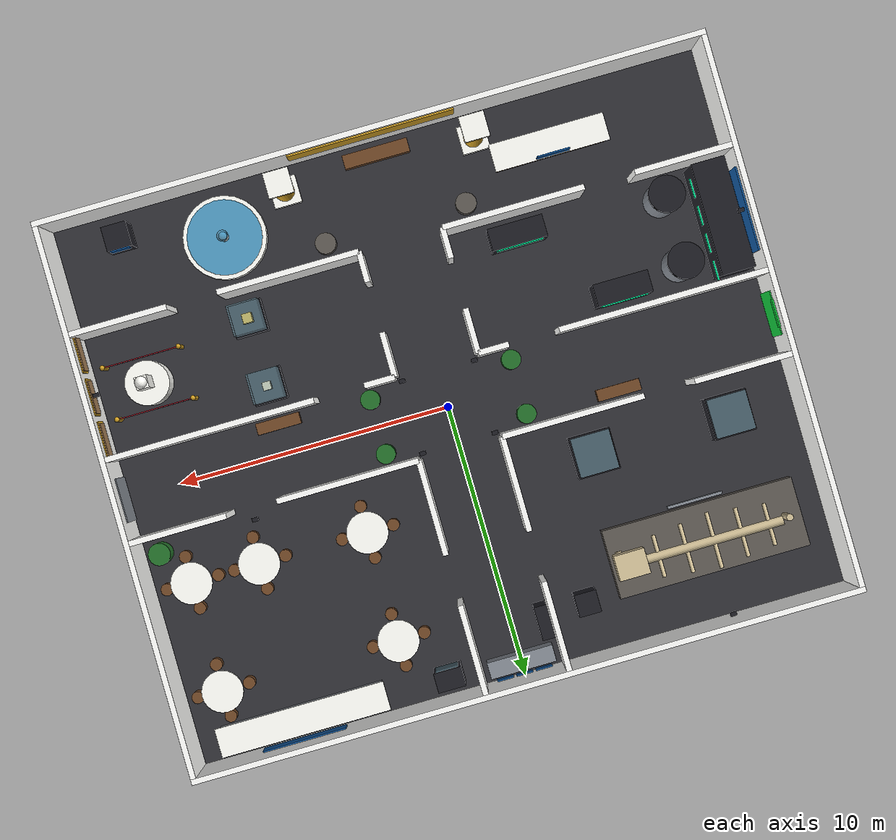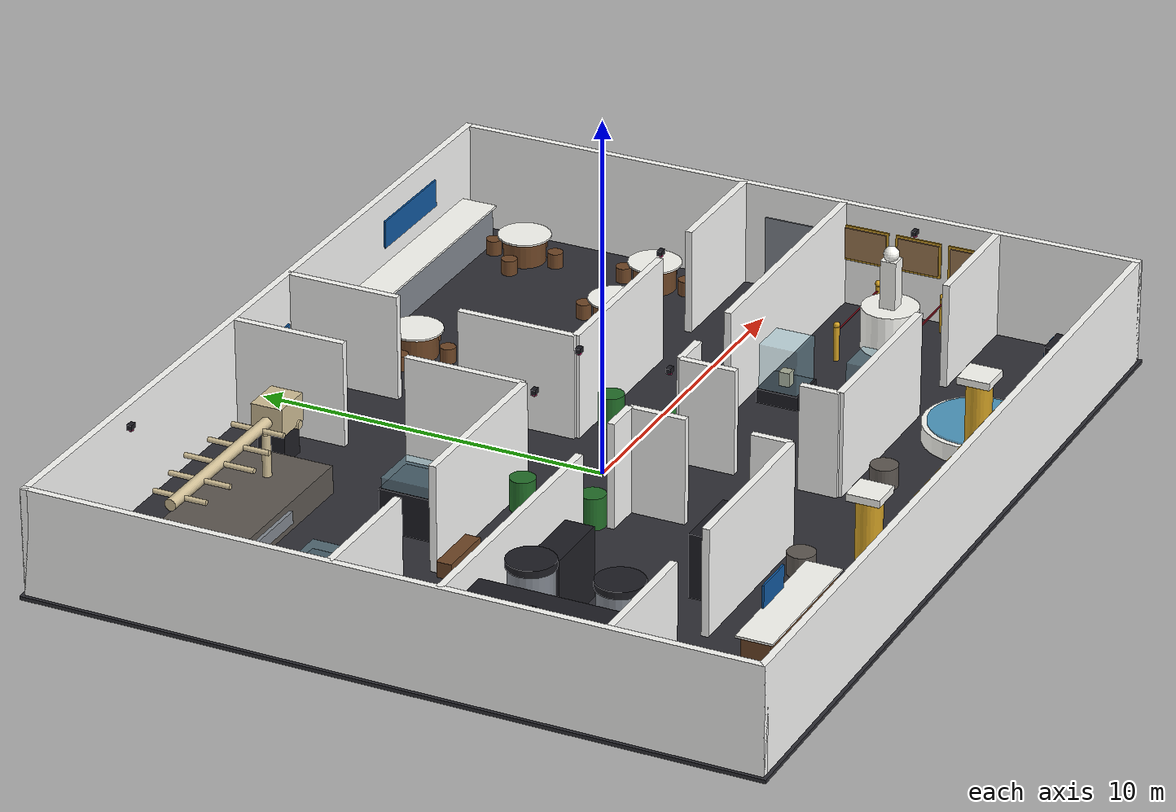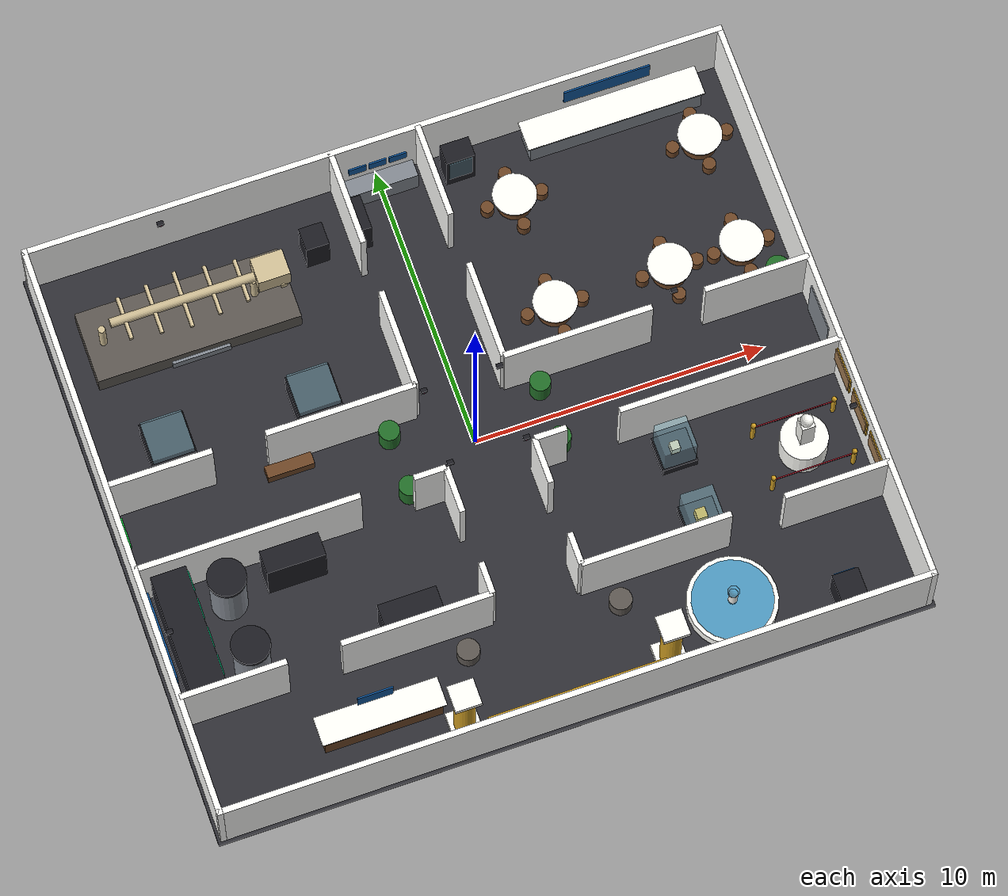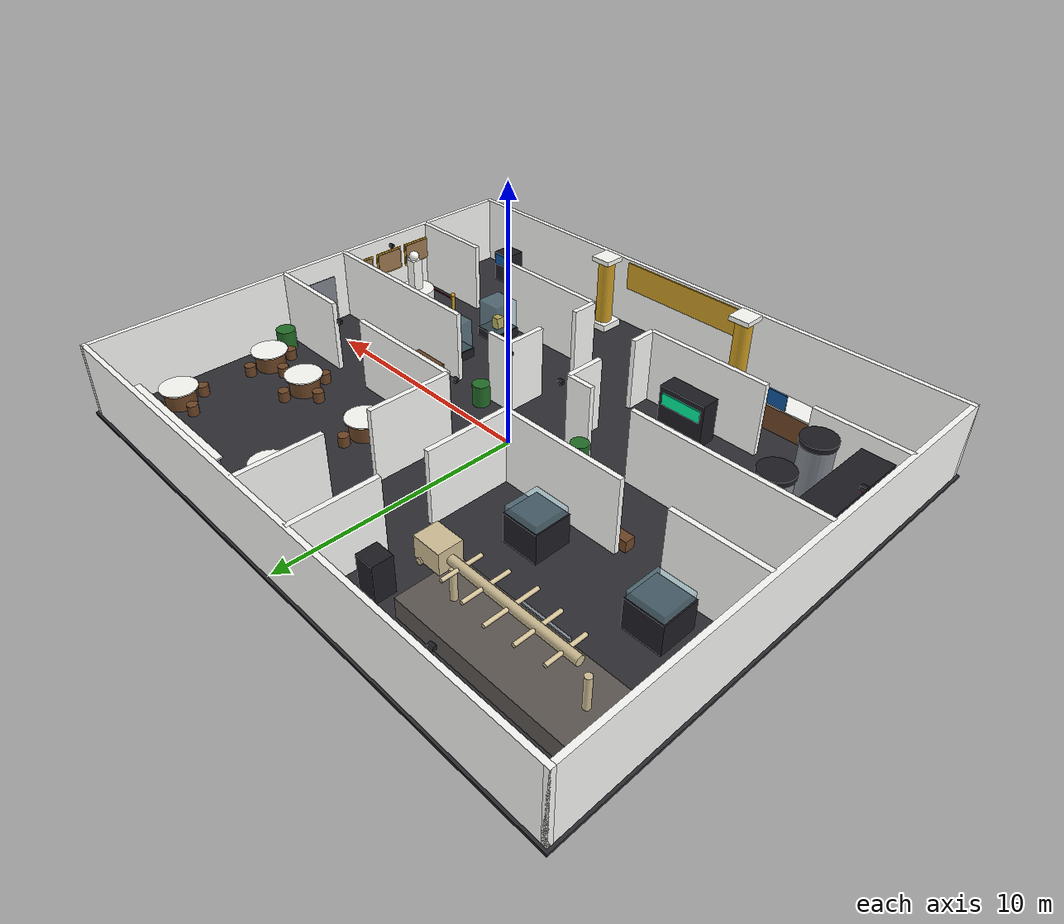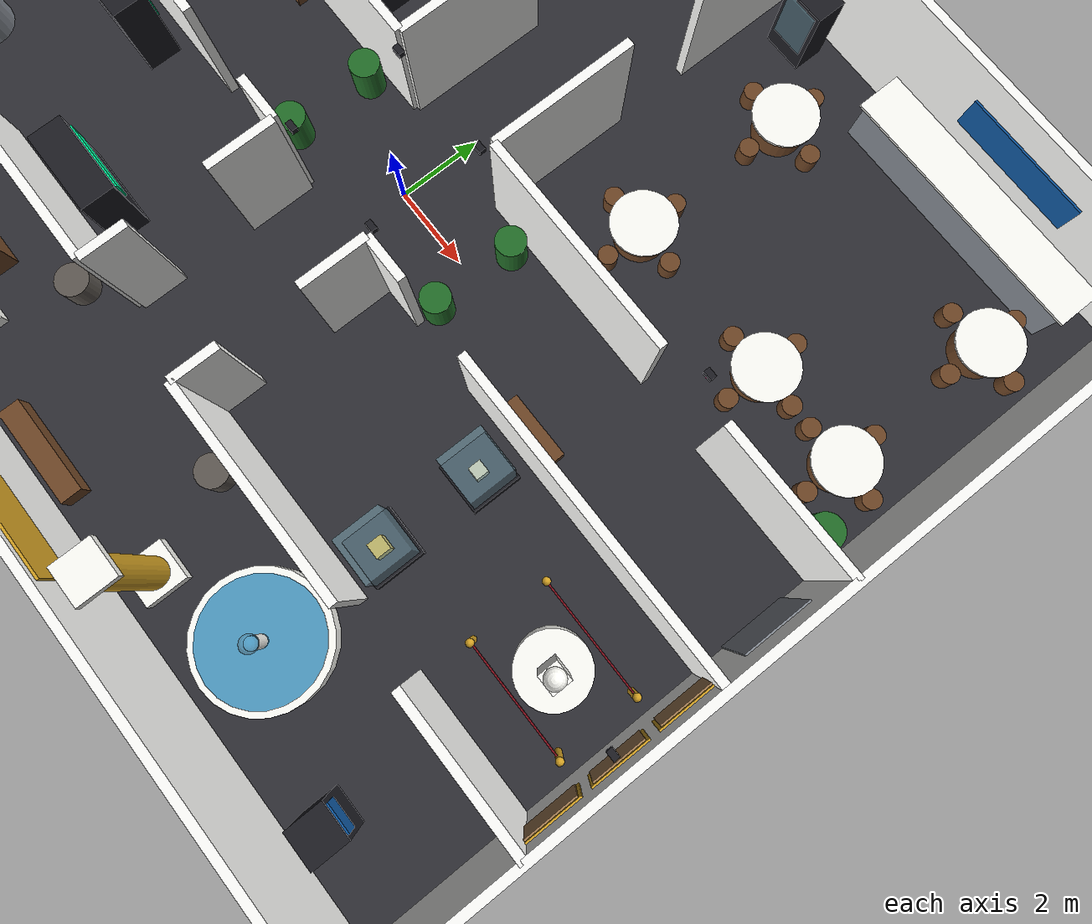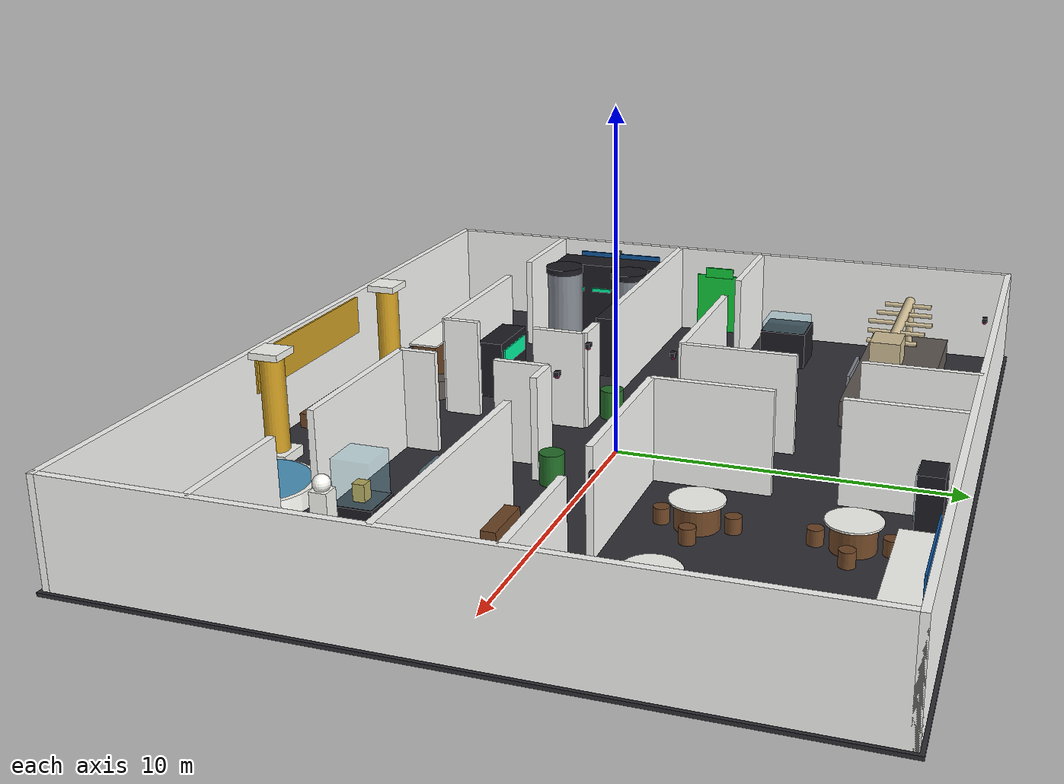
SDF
<?xml version="1.0" ?>
<sdf version="1.9">
  <world name="museum_world">

    <!-- Generated by tools/generate_world.py - DO NOT EDIT BY HAND -->

    <plugin filename="gz-sim-physics-system" name="gz::sim::systems::Physics"/>
    <plugin filename="gz-sim-user-commands-system" name="gz::sim::systems::UserCommands"/>
    <plugin filename="gz-sim-scene-broadcaster-system" name="gz::sim::systems::SceneBroadcaster"/>
    <plugin filename="gz-sim-sensors-system" name="gz::sim::systems::Sensors">
      <!-- ogre2 needs a real GPU.  On a VM with software rendering,
           launch with:  render_engine:=ogre -->
      <render_engine>ogre2</render_engine>
    </plugin>

    <!-- real_time_factor 0 = run as fast as the machine allows.
         Set it to 1.0 if you want wall-clock pacing for a demo video. -->
    <physics name="2ms" type="ignored">
      <max_step_size>0.002</max_step_size>
      <real_time_factor>0</real_time_factor>
    </physics>

    <scene>
      <ambient>0.55 0.55 0.58 1</ambient>
      <background>0.05 0.06 0.09 1</background>
      <shadows>true</shadows>
    </scene>

    <light type="directional" name="sun">
      <cast_shadows>true</cast_shadows>
      <pose>0 0 12 0 0 0</pose>
      <diffuse>0.75 0.75 0.72 1</diffuse>
      <specular>0.25 0.25 0.25 1</specular>
      <direction>-0.4 0.3 -0.9</direction>
    </light>
    <light type="point" name="ceiling_0">
      <pose>0 -8 2.8 0 0 0</pose>
      <diffuse>0.9 0.85 0.7 1</diffuse>
      <specular>0.2 0.2 0.2 1</specular>
      <attenuation><range>14</range><linear>0.10</linear><constant>0.4</constant><quadratic>0.005</quadratic></attenuation>
      <cast_shadows>false</cast_shadows>
    </light>
    <light type="point" name="ceiling_1">
      <pose>-7 -3.75 2.8 0 0 0</pose>
      <diffuse>0.5 0.8 0.9 1</diffuse>
      <specular>0.2 0.2 0.2 1</specular>
      <attenuation><range>14</range><linear>0.10</linear><constant>0.4</constant><quadratic>0.005</quadratic></attenuation>
      <cast_shadows>false</cast_shadows>
    </light>
    <light type="point" name="ceiling_2">
      <pose>8 -3.75 2.8 0 0 0</pose>
      <diffuse>0.95 0.9 0.8 1</diffuse>
      <specular>0.2 0.2 0.2 1</specular>
      <attenuation><range>14</range><linear>0.10</linear><constant>0.4</constant><quadratic>0.005</quadratic></attenuation>
      <cast_shadows>false</cast_shadows>
    </light>
    <light type="point" name="ceiling_3">
      <pose>-7 6 2.8 0 0 0</pose>
      <diffuse>0.9 0.8 0.6 1</diffuse>
      <specular>0.2 0.2 0.2 1</specular>
      <attenuation><range>14</range><linear>0.10</linear><constant>0.4</constant><quadratic>0.005</quadratic></attenuation>
      <cast_shadows>false</cast_shadows>
    </light>
    <light type="point" name="ceiling_4">
      <pose>7 6 2.8 0 0 0</pose>
      <diffuse>0.85 0.9 0.85 1</diffuse>
      <specular>0.2 0.2 0.2 1</specular>
      <attenuation><range>14</range><linear>0.10</linear><constant>0.4</constant><quadratic>0.005</quadratic></attenuation>
      <cast_shadows>false</cast_shadows>
    </light>
    <light type="point" name="ceiling_5">
      <pose>0 0 2.8 0 0 0</pose>
      <diffuse>0.8 0.8 0.85 1</diffuse>
      <specular>0.2 0.2 0.2 1</specular>
      <attenuation><range>14</range><linear>0.10</linear><constant>0.4</constant><quadratic>0.005</quadratic></attenuation>
      <cast_shadows>false</cast_shadows>
    </light>
    <light type="point" name="ceiling_6">
      <pose>0 8 2.8 0 0 0</pose>
      <diffuse>0.6 0.75 0.9 1</diffuse>
      <specular>0.2 0.2 0.2 1</specular>
      <attenuation><range>14</range><linear>0.10</linear><constant>0.4</constant><quadratic>0.005</quadratic></attenuation>
      <cast_shadows>false</cast_shadows>
    </light>

    <model name="centennial_robotics_museum">
      <static>true</static>
      <link name="floor">
        <pose>0 0 -0.05 0 0 0.0</pose>
        <visual name="visual">
          <geometry>
            <box><size>24.4 20.4 0.1</size></box>
          </geometry>
          <material>
            <ambient>0.16 0.16 0.18 1.0</ambient>
            <diffuse>0.184 0.184 0.207 1.0</diffuse>
            <specular>0.45 0.45 0.5 1</specular>
            <emissive>0.0 0.0 0.0 1</emissive>
          </material>
        </visual>
        <collision name="collision">
          <geometry>
            <box><size>24.4 20.4 0.1</size></box>
          </geometry>
        </collision>
      </link>
      <link name="outer_s_0">
        <pose>0.0 -10.0 1.5 0 0 0.0</pose>
        <visual name="visual">
          <geometry>
            <box><size>24.2 0.2 3.0</size></box>
          </geometry>
          <material>
            <ambient>0.88 0.88 0.86 1.0</ambient>
            <diffuse>1.0 1.0 0.9889999999999999 1.0</diffuse>
            <specular>0.1 0.1 0.1 1</specular>
            <emissive>0.0 0.0 0.0 1</emissive>
          </material>
        </visual>
        <collision name="collision">
          <geometry>
            <box><size>24.2 0.2 3.0</size></box>
          </geometry>
        </collision>
      </link>
      <link name="outer_n_0">
        <pose>0.0 10.0 1.5 0 0 0.0</pose>
        <visual name="visual">
          <geometry>
            <box><size>24.2 0.2 3.0</size></box>
          </geometry>
          <material>
            <ambient>0.88 0.88 0.86 1.0</ambient>
            <diffuse>1.0 1.0 0.9889999999999999 1.0</diffuse>
            <specular>0.1 0.1 0.1 1</specular>
            <emissive>0.0 0.0 0.0 1</emissive>
          </material>
        </visual>
        <collision name="collision">
          <geometry>
            <box><size>24.2 0.2 3.0</size></box>
          </geometry>
        </collision>
      </link>
      <link name="outer_w_0">
        <pose>-12.0 0.0 1.5 0 0 0.0</pose>
        <visual name="visual">
          <geometry>
            <box><size>0.2 20.2 3.0</size></box>
          </geometry>
          <material>
            <ambient>0.88 0.88 0.86 1.0</ambient>
            <diffuse>1.0 1.0 0.9889999999999999 1.0</diffuse>
            <specular>0.1 0.1 0.1 1</specular>
            <emissive>0.0 0.0 0.0 1</emissive>
          </material>
        </visual>
        <collision name="collision">
          <geometry>
            <box><size>0.2 20.2 3.0</size></box>
          </geometry>
        </collision>
      </link>
      <link name="outer_e_0">
        <pose>12.0 0.0 1.5 0 0 0.0</pose>
        <visual name="visual">
          <geometry>
            <box><size>0.2 20.2 3.0</size></box>
          </geometry>
          <material>
            <ambient>0.88 0.88 0.86 1.0</ambient>
            <diffuse>1.0 1.0 0.9889999999999999 1.0</diffuse>
            <specular>0.1 0.1 0.1 1</specular>
            <emissive>0.0 0.0 0.0 1</emissive>
          </material>
        </visual>
        <collision name="collision">
          <geometry>
            <box><size>0.2 20.2 3.0</size></box>
          </geometry>
        </collision>
      </link>
      <link name="div_s_0">
        <pose>-10.2 -6.0 1.5 0 0 0.0</pose>
        <visual name="visual">
          <geometry>
            <box><size>3.5999999999999996 0.2 3.0</size></box>
          </geometry>
          <material>
            <ambient>0.88 0.88 0.86 1.0</ambient>
            <diffuse>1.0 1.0 0.9889999999999999 1.0</diffuse>
            <specular>0.1 0.1 0.1 1</specular>
            <emissive>0.0 0.0 0.0 1</emissive>
          </material>
        </visual>
        <collision name="collision">
          <geometry>
            <box><size>3.5999999999999996 0.2 3.0</size></box>
          </geometry>
        </collision>
      </link>
      <link name="div_s_1">
        <pose>-4.050000000000001 -6.0 1.5 0 0 0.0</pose>
        <visual name="visual">
          <geometry>
            <box><size>5.1000000000000005 0.2 3.0</size></box>
          </geometry>
          <material>
            <ambient>0.88 0.88 0.86 1.0</ambient>
            <diffuse>1.0 1.0 0.9889999999999999 1.0</diffuse>
            <specular>0.1 0.1 0.1 1</specular>
            <emissive>0.0 0.0 0.0 1</emissive>
          </material>
        </visual>
        <collision name="collision">
          <geometry>
            <box><size>5.1000000000000005 0.2 3.0</size></box>
          </geometry>
        </collision>
      </link>
      <link name="div_s_2">
        <pose>4.050000000000001 -6.0 1.5 0 0 0.0</pose>
        <visual name="visual">
          <geometry>
            <box><size>5.1000000000000005 0.2 3.0</size></box>
          </geometry>
          <material>
            <ambient>0.88 0.88 0.86 1.0</ambient>
            <diffuse>1.0 1.0 0.9889999999999999 1.0</diffuse>
            <specular>0.1 0.1 0.1 1</specular>
            <emissive>0.0 0.0 0.0 1</emissive>
          </material>
        </visual>
        <collision name="collision">
          <geometry>
            <box><size>5.1000000000000005 0.2 3.0</size></box>
          </geometry>
        </collision>
      </link>
      <link name="div_s_3">
        <pose>10.2 -6.0 1.5 0 0 0.0</pose>
        <visual name="visual">
          <geometry>
            <box><size>3.5999999999999996 0.2 3.0</size></box>
          </geometry>
          <material>
            <ambient>0.88 0.88 0.86 1.0</ambient>
            <diffuse>1.0 1.0 0.9889999999999999 1.0</diffuse>
            <specular>0.1 0.1 0.1 1</specular>
            <emissive>0.0 0.0 0.0 1</emissive>
          </material>
        </visual>
        <collision name="collision">
          <geometry>
            <box><size>3.5999999999999996 0.2 3.0</size></box>
          </geometry>
        </collision>
      </link>
      <link name="div_m_0">
        <pose>-8.2 -1.5 1.5 0 0 0.0</pose>
        <visual name="visual">
          <geometry>
            <box><size>7.6 0.2 3.0</size></box>
          </geometry>
          <material>
            <ambient>0.88 0.88 0.86 1.0</ambient>
            <diffuse>1.0 1.0 0.9889999999999999 1.0</diffuse>
            <specular>0.1 0.1 0.1 1</specular>
            <emissive>0.0 0.0 0.0 1</emissive>
          </material>
        </visual>
        <collision name="collision">
          <geometry>
            <box><size>7.6 0.2 3.0</size></box>
          </geometry>
        </collision>
      </link>
      <link name="div_m_1">
        <pose>-2.0500000000000003 -1.5 1.5 0 0 0.0</pose>
        <visual name="visual">
          <geometry>
            <box><size>1.1000000000000005 0.2 3.0</size></box>
          </geometry>
          <material>
            <ambient>0.88 0.88 0.86 1.0</ambient>
            <diffuse>1.0 1.0 0.9889999999999999 1.0</diffuse>
            <specular>0.1 0.1 0.1 1</specular>
            <emissive>0.0 0.0 0.0 1</emissive>
          </material>
        </visual>
        <collision name="collision">
          <geometry>
            <box><size>1.1000000000000005 0.2 3.0</size></box>
          </geometry>
        </collision>
      </link>
      <link name="div_m_2">
        <pose>2.0500000000000003 -1.5 1.5 0 0 0.0</pose>
        <visual name="visual">
          <geometry>
            <box><size>1.1000000000000005 0.2 3.0</size></box>
          </geometry>
          <material>
            <ambient>0.88 0.88 0.86 1.0</ambient>
            <diffuse>1.0 1.0 0.9889999999999999 1.0</diffuse>
            <specular>0.1 0.1 0.1 1</specular>
            <emissive>0.0 0.0 0.0 1</emissive>
          </material>
        </visual>
        <collision name="collision">
          <geometry>
            <box><size>1.1000000000000005 0.2 3.0</size></box>
          </geometry>
        </collision>
      </link>
      <link name="div_m_3">
        <pose>8.2 -1.5 1.5 0 0 0.0</pose>
        <visual name="visual">
          <geometry>
            <box><size>7.6 0.2 3.0</size></box>
          </geometry>
          <material>
            <ambient>0.88 0.88 0.86 1.0</ambient>
            <diffuse>1.0 1.0 0.9889999999999999 1.0</diffuse>
            <specular>0.1 0.1 0.1 1</specular>
            <emissive>0.0 0.0 0.0 1</emissive>
          </material>
        </visual>
        <collision name="collision">
          <geometry>
            <box><size>7.6 0.2 3.0</size></box>
          </geometry>
        </collision>
      </link>
      <link name="div_n_0">
        <pose>-10.2 1.5 1.5 0 0 0.0</pose>
        <visual name="visual">
          <geometry>
            <box><size>3.5999999999999996 0.2 3.0</size></box>
          </geometry>
          <material>
            <ambient>0.88 0.88 0.86 1.0</ambient>
            <diffuse>1.0 1.0 0.9889999999999999 1.0</diffuse>
            <specular>0.1 0.1 0.1 1</specular>
            <emissive>0.0 0.0 0.0 1</emissive>
          </material>
        </visual>
        <collision name="collision">
          <geometry>
            <box><size>3.5999999999999996 0.2 3.0</size></box>
          </geometry>
        </collision>
      </link>
      <link name="div_n_1">
        <pose>-4.050000000000001 1.5 1.5 0 0 0.0</pose>
        <visual name="visual">
          <geometry>
            <box><size>5.1000000000000005 0.2 3.0</size></box>
          </geometry>
          <material>
            <ambient>0.88 0.88 0.86 1.0</ambient>
            <diffuse>1.0 1.0 0.9889999999999999 1.0</diffuse>
            <specular>0.1 0.1 0.1 1</specular>
            <emissive>0.0 0.0 0.0 1</emissive>
          </material>
        </visual>
        <collision name="collision">
          <geometry>
            <box><size>5.1000000000000005 0.2 3.0</size></box>
          </geometry>
        </collision>
      </link>
      <link name="div_n_2">
        <pose>4.050000000000001 1.5 1.5 0 0 0.0</pose>
        <visual name="visual">
          <geometry>
            <box><size>5.1000000000000005 0.2 3.0</size></box>
          </geometry>
          <material>
            <ambient>0.88 0.88 0.86 1.0</ambient>
            <diffuse>1.0 1.0 0.9889999999999999 1.0</diffuse>
            <specular>0.1 0.1 0.1 1</specular>
            <emissive>0.0 0.0 0.0 1</emissive>
          </material>
        </visual>
        <collision name="collision">
          <geometry>
            <box><size>5.1000000000000005 0.2 3.0</size></box>
          </geometry>
        </collision>
      </link>
      <link name="div_n_3">
        <pose>10.2 1.5 1.5 0 0 0.0</pose>
        <visual name="visual">
          <geometry>
            <box><size>3.5999999999999996 0.2 3.0</size></box>
          </geometry>
          <material>
            <ambient>0.88 0.88 0.86 1.0</ambient>
            <diffuse>1.0 1.0 0.9889999999999999 1.0</diffuse>
            <specular>0.1 0.1 0.1 1</specular>
            <emissive>0.0 0.0 0.0 1</emissive>
          </material>
        </visual>
        <collision name="collision">
          <geometry>
            <box><size>3.5999999999999996 0.2 3.0</size></box>
          </geometry>
        </collision>
      </link>
      <link name="cor_sw_0">
        <pose>-1.5 -5.45 1.5 0 0 0.0</pose>
        <visual name="visual">
          <geometry>
            <box><size>0.2 1.0999999999999996 3.0</size></box>
          </geometry>
          <material>
            <ambient>0.88 0.88 0.86 1.0</ambient>
            <diffuse>1.0 1.0 0.9889999999999999 1.0</diffuse>
            <specular>0.1 0.1 0.1 1</specular>
            <emissive>0.0 0.0 0.0 1</emissive>
          </material>
        </visual>
        <collision name="collision">
          <geometry>
            <box><size>0.2 1.0999999999999996 3.0</size></box>
          </geometry>
        </collision>
      </link>
      <link name="cor_sw_1">
        <pose>-1.5 -2.3000000000000003 1.5 0 0 0.0</pose>
        <visual name="visual">
          <geometry>
            <box><size>0.2 1.6000000000000005 3.0</size></box>
          </geometry>
          <material>
            <ambient>0.88 0.88 0.86 1.0</ambient>
            <diffuse>1.0 1.0 0.9889999999999999 1.0</diffuse>
            <specular>0.1 0.1 0.1 1</specular>
            <emissive>0.0 0.0 0.0 1</emissive>
          </material>
        </visual>
        <collision name="collision">
          <geometry>
            <box><size>0.2 1.6000000000000005 3.0</size></box>
          </geometry>
        </collision>
      </link>
      <link name="cor_se_0">
        <pose>1.5 -5.45 1.5 0 0 0.0</pose>
        <visual name="visual">
          <geometry>
            <box><size>0.2 1.0999999999999996 3.0</size></box>
          </geometry>
          <material>
            <ambient>0.88 0.88 0.86 1.0</ambient>
            <diffuse>1.0 1.0 0.9889999999999999 1.0</diffuse>
            <specular>0.1 0.1 0.1 1</specular>
            <emissive>0.0 0.0 0.0 1</emissive>
          </material>
        </visual>
        <collision name="collision">
          <geometry>
            <box><size>0.2 1.0999999999999996 3.0</size></box>
          </geometry>
        </collision>
      </link>
      <link name="cor_se_1">
        <pose>1.5 -2.3000000000000003 1.5 0 0 0.0</pose>
        <visual name="visual">
          <geometry>
            <box><size>0.2 1.6000000000000005 3.0</size></box>
          </geometry>
          <material>
            <ambient>0.88 0.88 0.86 1.0</ambient>
            <diffuse>1.0 1.0 0.9889999999999999 1.0</diffuse>
            <specular>0.1 0.1 0.1 1</specular>
            <emissive>0.0 0.0 0.0 1</emissive>
          </material>
        </visual>
        <collision name="collision">
          <geometry>
            <box><size>0.2 1.6000000000000005 3.0</size></box>
          </geometry>
        </collision>
      </link>
      <link name="cor_nw_0">
        <pose>-1.5 3.2 1.5 0 0 0.0</pose>
        <visual name="visual">
          <geometry>
            <box><size>0.2 3.4000000000000004 3.0</size></box>
          </geometry>
          <material>
            <ambient>0.88 0.88 0.86 1.0</ambient>
            <diffuse>1.0 1.0 0.9889999999999999 1.0</diffuse>
            <specular>0.1 0.1 0.1 1</specular>
            <emissive>0.0 0.0 0.0 1</emissive>
          </material>
        </visual>
        <collision name="collision">
          <geometry>
            <box><size>0.2 3.4000000000000004 3.0</size></box>
          </geometry>
        </collision>
      </link>
      <link name="cor_nw_1">
        <pose>-1.5 8.35 1.5 0 0 0.0</pose>
        <visual name="visual">
          <geometry>
            <box><size>0.2 3.3 3.0</size></box>
          </geometry>
          <material>
            <ambient>0.88 0.88 0.86 1.0</ambient>
            <diffuse>1.0 1.0 0.9889999999999999 1.0</diffuse>
            <specular>0.1 0.1 0.1 1</specular>
            <emissive>0.0 0.0 0.0 1</emissive>
          </material>
        </visual>
        <collision name="collision">
          <geometry>
            <box><size>0.2 3.3 3.0</size></box>
          </geometry>
        </collision>
      </link>
      <link name="cor_ne_0">
        <pose>1.5 3.2 1.5 0 0 0.0</pose>
        <visual name="visual">
          <geometry>
            <box><size>0.2 3.4000000000000004 3.0</size></box>
          </geometry>
          <material>
            <ambient>0.88 0.88 0.86 1.0</ambient>
            <diffuse>1.0 1.0 0.9889999999999999 1.0</diffuse>
            <specular>0.1 0.1 0.1 1</specular>
            <emissive>0.0 0.0 0.0 1</emissive>
          </material>
        </visual>
        <collision name="collision">
          <geometry>
            <box><size>0.2 3.4000000000000004 3.0</size></box>
          </geometry>
        </collision>
      </link>
      <link name="cor_ne_1">
        <pose>1.5 8.35 1.5 0 0 0.0</pose>
        <visual name="visual">
          <geometry>
            <box><size>0.2 3.3 3.0</size></box>
          </geometry>
          <material>
            <ambient>0.88 0.88 0.86 1.0</ambient>
            <diffuse>1.0 1.0 0.9889999999999999 1.0</diffuse>
            <specular>0.1 0.1 0.1 1</specular>
            <emissive>0.0 0.0 0.0 1</emissive>
          </material>
        </visual>
        <collision name="collision">
          <geometry>
            <box><size>0.2 3.3 3.0</size></box>
          </geometry>
        </collision>
      </link>
      <link name="reception_desk">
        <pose>-6.0 -8.0 0.55 0 0 0.0</pose>
        <visual name="visual">
          <geometry>
            <box><size>4.0 0.8 1.1</size></box>
          </geometry>
          <material>
            <ambient>0.38 0.24 0.13 1.0</ambient>
            <diffuse>0.43699999999999994 0.27599999999999997 0.1495 1.0</diffuse>
            <specular>0.2 0.2 0.2 1</specular>
            <emissive>0.0 0.0 0.0 1</emissive>
          </material>
        </visual>
        <collision name="collision">
          <geometry>
            <box><size>4.0 0.8 1.1</size></box>
          </geometry>
        </collision>
      </link>
      <link name="reception_top">
        <pose>-6.0 -8.0 1.13 0 0 0.0</pose>
        <visual name="visual">
          <geometry>
            <box><size>4.2 1.0 0.06</size></box>
          </geometry>
          <material>
            <ambient>0.9 0.89 0.85 1.0</ambient>
            <diffuse>1.0 1.0 0.9774999999999999 1.0</diffuse>
            <specular>0.8 0.8 0.8 1</specular>
            <emissive>0.0 0.0 0.0 1</emissive>
          </material>
        </visual>
        <collision name="collision">
          <geometry>
            <box><size>4.2 1.0 0.06</size></box>
          </geometry>
        </collision>
      </link>
      <link name="reception_screen">
        <pose>-6.0 -7.55 1.45 0 0 0.0</pose>
        <visual name="visual">
          <geometry>
            <box><size>1.2 0.05 0.7</size></box>
          </geometry>
          <material>
            <ambient>0.05 0.3 0.55 1.0</ambient>
            <diffuse>0.057499999999999996 0.345 0.6325 1.0</diffuse>
            <specular>0.1 0.1 0.1 1</specular>
            <emissive>0.03 0.25 0.45 1</emissive>
          </material>
        </visual>
      </link>
      <link name="fountain_basin">
        <pose>6.0 -8.0 0.25 0 0 0</pose>
        <visual name="visual">
          <geometry>
            <cylinder><radius>1.5</radius><length>0.5</length></cylinder>
          </geometry>
          <material>
            <ambient>0.9 0.89 0.85 1.0</ambient>
            <diffuse>1.0 1.0 0.9774999999999999 1.0</diffuse>
            <specular>0.8 0.8 0.8 1</specular>
            <emissive>0.0 0.0 0.0 1</emissive>
          </material>
        </visual>
        <collision name="collision">
          <geometry>
            <cylinder><radius>1.5</radius><length>0.5</length></cylinder>
          </geometry>
        </collision>
      </link>
      <link name="fountain_water">
        <pose>6.0 -8.0 0.52 0 0 0</pose>
        <visual name="visual">
          <geometry>
            <cylinder><radius>1.35</radius><length>0.08</length></cylinder>
          </geometry>
          <material>
            <ambient>0.05 0.42 0.62 0.7</ambient>
            <diffuse>0.057499999999999996 0.48299999999999993 0.713 0.7</diffuse>
            <specular>0.1 0.1 0.1 1</specular>
            <emissive>0.02 0.16 0.26 1</emissive>
          </material>
          <transparency>0.30</transparency>
        </visual>
      </link>
      <link name="fountain_spout">
        <pose>6.0 -8.0 0.85 0 0 0</pose>
        <visual name="visual">
          <geometry>
            <cylinder><radius>0.15</radius><length>0.7</length></cylinder>
          </geometry>
          <material>
            <ambient>0.9 0.89 0.85 1.0</ambient>
            <diffuse>1.0 1.0 0.9774999999999999 1.0</diffuse>
            <specular>0.8 0.8 0.8 1</specular>
            <emissive>0.0 0.0 0.0 1</emissive>
          </material>
        </visual>
      </link>
      <link name="fountain_droplet">
        <pose>6.0 -8.0 1.35 0 0 0.0</pose>
        <visual name="visual">
          <geometry>
            <sphere><radius>0.2</radius></sphere>
          </geometry>
          <material>
            <ambient>0.05 0.42 0.62 0.7</ambient>
            <diffuse>0.057499999999999996 0.48299999999999993 0.713 0.7</diffuse>
            <specular>0.1 0.1 0.1 1</specular>
            <emissive>0.02 0.16 0.26 1</emissive>
          </material>
          <transparency>0.30</transparency>
        </visual>
      </link>
      <link name="pillar_l_base">
        <pose>-3.5 -9.0 0.15 0 0 0.0</pose>
        <visual name="visual">
          <geometry>
            <box><size>1.0 1.0 0.3</size></box>
          </geometry>
          <material>
            <ambient>0.9 0.89 0.85 1.0</ambient>
            <diffuse>1.0 1.0 0.9774999999999999 1.0</diffuse>
            <specular>0.8 0.8 0.8 1</specular>
            <emissive>0.0 0.0 0.0 1</emissive>
          </material>
        </visual>
        <collision name="collision">
          <geometry>
            <box><size>1.0 1.0 0.3</size></box>
          </geometry>
        </collision>
      </link>
      <link name="pillar_l">
        <pose>-3.5 -9.0 1.65 0 0 0</pose>
        <visual name="visual">
          <geometry>
            <cylinder><radius>0.35</radius><length>3.0</length></cylinder>
          </geometry>
          <material>
            <ambient>0.72 0.55 0.12 1.0</ambient>
            <diffuse>0.828 0.6325 0.13799999999999998 1.0</diffuse>
            <specular>1.0 0.9 0.6 1</specular>
            <emissive>0.0 0.0 0.0 1</emissive>
          </material>
        </visual>
        <collision name="collision">
          <geometry>
            <cylinder><radius>0.35</radius><length>3.0</length></cylinder>
          </geometry>
        </collision>
      </link>
      <link name="pillar_l_cap">
        <pose>-3.5 -9.0 3.2 0 0 0.0</pose>
        <visual name="visual">
          <geometry>
            <box><size>0.9 0.9 0.2</size></box>
          </geometry>
          <material>
            <ambient>0.9 0.89 0.85 1.0</ambient>
            <diffuse>1.0 1.0 0.9774999999999999 1.0</diffuse>
            <specular>0.8 0.8 0.8 1</specular>
            <emissive>0.0 0.0 0.0 1</emissive>
          </material>
        </visual>
        <collision name="collision">
          <geometry>
            <box><size>0.9 0.9 0.2</size></box>
          </geometry>
        </collision>
      </link>
      <link name="pillar_r_base">
        <pose>3.5 -9.0 0.15 0 0 0.0</pose>
        <visual name="visual">
          <geometry>
            <box><size>1.0 1.0 0.3</size></box>
          </geometry>
          <material>
            <ambient>0.9 0.89 0.85 1.0</ambient>
            <diffuse>1.0 1.0 0.9774999999999999 1.0</diffuse>
            <specular>0.8 0.8 0.8 1</specular>
            <emissive>0.0 0.0 0.0 1</emissive>
          </material>
        </visual>
        <collision name="collision">
          <geometry>
            <box><size>1.0 1.0 0.3</size></box>
          </geometry>
        </collision>
      </link>
      <link name="pillar_r">
        <pose>3.5 -9.0 1.65 0 0 0</pose>
        <visual name="visual">
          <geometry>
            <cylinder><radius>0.35</radius><length>3.0</length></cylinder>
          </geometry>
          <material>
            <ambient>0.72 0.55 0.12 1.0</ambient>
            <diffuse>0.828 0.6325 0.13799999999999998 1.0</diffuse>
            <specular>1.0 0.9 0.6 1</specular>
            <emissive>0.0 0.0 0.0 1</emissive>
          </material>
        </visual>
        <collision name="collision">
          <geometry>
            <cylinder><radius>0.35</radius><length>3.0</length></cylinder>
          </geometry>
        </collision>
      </link>
      <link name="pillar_r_cap">
        <pose>3.5 -9.0 3.2 0 0 0.0</pose>
        <visual name="visual">
          <geometry>
            <box><size>0.9 0.9 0.2</size></box>
          </geometry>
          <material>
            <ambient>0.9 0.89 0.85 1.0</ambient>
            <diffuse>1.0 1.0 0.9774999999999999 1.0</diffuse>
            <specular>0.8 0.8 0.8 1</specular>
            <emissive>0.0 0.0 0.0 1</emissive>
          </material>
        </visual>
        <collision name="collision">
          <geometry>
            <box><size>0.9 0.9 0.2</size></box>
          </geometry>
        </collision>
      </link>
      <link name="lobby_bench">
        <pose>0.0 -9.4 0.22 0 0 0.0</pose>
        <visual name="visual">
          <geometry>
            <box><size>2.4 0.5 0.45</size></box>
          </geometry>
          <material>
            <ambient>0.38 0.24 0.13 1.0</ambient>
            <diffuse>0.43699999999999994 0.27599999999999997 0.1495 1.0</diffuse>
            <specular>0.2 0.2 0.2 1</specular>
            <emissive>0.0 0.0 0.0 1</emissive>
          </material>
        </visual>
        <collision name="collision">
          <geometry>
            <box><size>2.4 0.5 0.45</size></box>
          </geometry>
        </collision>
      </link>
      <link name="info_kiosk">
        <pose>9.6 -9.0 0.7 0 0 0.0</pose>
        <visual name="visual">
          <geometry>
            <box><size>0.9 0.9 1.4</size></box>
          </geometry>
          <material>
            <ambient>0.1 0.1 0.12 1.0</ambient>
            <diffuse>0.11499999999999999 0.11499999999999999 0.13799999999999998 1.0</diffuse>
            <specular>0.3 0.3 0.3 1</specular>
            <emissive>0.0 0.0 0.0 1</emissive>
          </material>
        </visual>
        <collision name="collision">
          <geometry>
            <box><size>0.9 0.9 1.4</size></box>
          </geometry>
        </collision>
      </link>
      <link name="kiosk_screen">
        <pose>9.6 -8.53 1.1 0 0 0.0</pose>
        <visual name="visual">
          <geometry>
            <box><size>0.7 0.05 0.5</size></box>
          </geometry>
          <material>
            <ambient>0.05 0.3 0.55 1.0</ambient>
            <diffuse>0.057499999999999996 0.345 0.6325 1.0</diffuse>
            <specular>0.1 0.1 0.1 1</specular>
            <emissive>0.03 0.25 0.45 1</emissive>
          </material>
        </visual>
      </link>
      <link name="welcome_banner">
        <pose>0.0 -9.85 2.3 0 0 0.0</pose>
        <visual name="visual">
          <geometry>
            <box><size>6.0 0.06 1.2</size></box>
          </geometry>
          <material>
            <ambient>0.72 0.55 0.12 1.0</ambient>
            <diffuse>0.828 0.6325 0.13799999999999998 1.0</diffuse>
            <specular>1.0 0.9 0.6 1</specular>
            <emissive>0.0 0.0 0.0 1</emissive>
          </material>
        </visual>
      </link>
      <link name="planter_lobby_m3">
        <pose>-2.6 -6.8 0.3 0 0 0</pose>
        <visual name="visual">
          <geometry>
            <cylinder><radius>0.38</radius><length>0.6</length></cylinder>
          </geometry>
          <material>
            <ambient>0.32 0.3 0.28 1.0</ambient>
            <diffuse>0.368 0.345 0.322 1.0</diffuse>
            <specular>0.1 0.1 0.1 1</specular>
            <emissive>0.0 0.0 0.0 1</emissive>
          </material>
        </visual>
        <collision name="collision">
          <geometry>
            <cylinder><radius>0.38</radius><length>0.6</length></cylinder>
          </geometry>
        </collision>
      </link>
      <link name="planter_lobby_p3">
        <pose>2.6 -6.8 0.3 0 0 0</pose>
        <visual name="visual">
          <geometry>
            <cylinder><radius>0.38</radius><length>0.6</length></cylinder>
          </geometry>
          <material>
            <ambient>0.32 0.3 0.28 1.0</ambient>
            <diffuse>0.368 0.345 0.322 1.0</diffuse>
            <specular>0.1 0.1 0.1 1</specular>
            <emissive>0.0 0.0 0.0 1</emissive>
          </material>
        </visual>
        <collision name="collision">
          <geometry>
            <cylinder><radius>0.38</radius><length>0.6</length></cylinder>
          </geometry>
        </collision>
      </link>
      <link name="mainframe">
        <pose>-11.0 -3.75 1.25 0 0 0.0</pose>
        <visual name="visual">
          <geometry>
            <box><size>1.2 4.0 2.5</size></box>
          </geometry>
          <material>
            <ambient>0.1 0.1 0.12 1.0</ambient>
            <diffuse>0.11499999999999999 0.11499999999999999 0.13799999999999998 1.0</diffuse>
            <specular>0.3 0.3 0.3 1</specular>
            <emissive>0.0 0.0 0.0 1</emissive>
          </material>
        </visual>
        <collision name="collision">
          <geometry>
            <box><size>1.2 4.0 2.5</size></box>
          </geometry>
        </collision>
      </link>
      <link name="mainframe_glow_0">
        <pose>-10.35 -5.0 1.6 0 0 0.0</pose>
        <visual name="visual">
          <geometry>
            <box><size>0.06 0.7 0.12</size></box>
          </geometry>
          <material>
            <ambient>0.0 0.85 0.55 1.0</ambient>
            <diffuse>0.0 0.9774999999999999 0.6325 1.0</diffuse>
            <specular>0.1 0.1 0.1 1</specular>
            <emissive>0.0 0.95 0.6 1</emissive>
          </material>
        </visual>
      </link>
      <link name="mainframe_glow_1">
        <pose>-10.35 -4.0 1.6 0 0 0.0</pose>
        <visual name="visual">
          <geometry>
            <box><size>0.06 0.7 0.12</size></box>
          </geometry>
          <material>
            <ambient>0.0 0.85 0.55 1.0</ambient>
            <diffuse>0.0 0.9774999999999999 0.6325 1.0</diffuse>
            <specular>0.1 0.1 0.1 1</specular>
            <emissive>0.0 0.95 0.6 1</emissive>
          </material>
        </visual>
      </link>
      <link name="mainframe_glow_2">
        <pose>-10.35 -3.0 1.6 0 0 0.0</pose>
        <visual name="visual">
          <geometry>
            <box><size>0.06 0.7 0.12</size></box>
          </geometry>
          <material>
            <ambient>0.0 0.85 0.55 1.0</ambient>
            <diffuse>0.0 0.9774999999999999 0.6325 1.0</diffuse>
            <specular>0.1 0.1 0.1 1</specular>
            <emissive>0.0 0.95 0.6 1</emissive>
          </material>
        </visual>
      </link>
      <link name="mainframe_glow_3">
        <pose>-10.35 -2.0 1.6 0 0 0.0</pose>
        <visual name="visual">
          <geometry>
            <box><size>0.06 0.7 0.12</size></box>
          </geometry>
          <material>
            <ambient>0.0 0.85 0.55 1.0</ambient>
            <diffuse>0.0 0.9774999999999999 0.6325 1.0</diffuse>
            <specular>0.1 0.1 0.1 1</specular>
            <emissive>0.0 0.95 0.6 1</emissive>
          </material>
        </visual>
      </link>
      <link name="cooling_tower_1">
        <pose>-9.3 -5.0 1.25 0 0 0</pose>
        <visual name="visual">
          <geometry>
            <cylinder><radius>0.6</radius><length>2.5</length></cylinder>
          </geometry>
          <material>
            <ambient>0.45 0.47 0.5 1.0</ambient>
            <diffuse>0.5175 0.5405 0.575 1.0</diffuse>
            <specular>0.7 0.7 0.7 1</specular>
            <emissive>0.0 0.0 0.0 1</emissive>
          </material>
        </visual>
        <collision name="collision">
          <geometry>
            <cylinder><radius>0.6</radius><length>2.5</length></cylinder>
          </geometry>
        </collision>
      </link>
      <link name="cooling_tower_2">
        <pose>-9.3 -2.6 1.25 0 0 0</pose>
        <visual name="visual">
          <geometry>
            <cylinder><radius>0.6</radius><length>2.5</length></cylinder>
          </geometry>
          <material>
            <ambient>0.45 0.47 0.5 1.0</ambient>
            <diffuse>0.5175 0.5405 0.575 1.0</diffuse>
            <specular>0.7 0.7 0.7 1</specular>
            <emissive>0.0 0.0 0.0 1</emissive>
          </material>
        </visual>
        <collision name="collision">
          <geometry>
            <cylinder><radius>0.6</radius><length>2.5</length></cylinder>
          </geometry>
        </collision>
      </link>
      <link name="cooling_cap_1">
        <pose>-9.3 -5.0 2.6 0 0 0</pose>
        <visual name="visual">
          <geometry>
            <cylinder><radius>0.65</radius><length>0.2</length></cylinder>
          </geometry>
          <material>
            <ambient>0.1 0.1 0.12 1.0</ambient>
            <diffuse>0.11499999999999999 0.11499999999999999 0.13799999999999998 1.0</diffuse>
            <specular>0.3 0.3 0.3 1</specular>
            <emissive>0.0 0.0 0.0 1</emissive>
          </material>
        </visual>
      </link>
      <link name="cooling_cap_2">
        <pose>-9.3 -2.6 2.6 0 0 0</pose>
        <visual name="visual">
          <geometry>
            <cylinder><radius>0.65</radius><length>0.2</length></cylinder>
          </geometry>
          <material>
            <ambient>0.1 0.1 0.12 1.0</ambient>
            <diffuse>0.11499999999999999 0.11499999999999999 0.13799999999999998 1.0</diffuse>
            <specular>0.3 0.3 0.3 1</specular>
            <emissive>0.0 0.0 0.0 1</emissive>
          </material>
        </visual>
      </link>
      <link name="server_rack_1">
        <pose>-7.0 -2.3 1.0 0 0 0.0</pose>
        <visual name="visual">
          <geometry>
            <box><size>2.0 0.8 2.0</size></box>
          </geometry>
          <material>
            <ambient>0.1 0.1 0.12 1.0</ambient>
            <diffuse>0.11499999999999999 0.11499999999999999 0.13799999999999998 1.0</diffuse>
            <specular>0.3 0.3 0.3 1</specular>
            <emissive>0.0 0.0 0.0 1</emissive>
          </material>
        </visual>
        <collision name="collision">
          <geometry>
            <box><size>2.0 0.8 2.0</size></box>
          </geometry>
        </collision>
      </link>
      <link name="server_rack_1_leds">
        <pose>-7.0 -1.88 1.4 0 0 0.0</pose>
        <visual name="visual">
          <geometry>
            <box><size>1.7 0.04 0.6</size></box>
          </geometry>
          <material>
            <ambient>0.0 0.85 0.55 1.0</ambient>
            <diffuse>0.0 0.9774999999999999 0.6325 1.0</diffuse>
            <specular>0.1 0.1 0.1 1</specular>
            <emissive>0.0 0.95 0.6 1</emissive>
          </material>
        </visual>
      </link>
      <link name="server_rack_2">
        <pose>-4.0 -5.2 0.9 0 0 0.0</pose>
        <visual name="visual">
          <geometry>
            <box><size>2.0 0.8 1.8</size></box>
          </geometry>
          <material>
            <ambient>0.1 0.1 0.12 1.0</ambient>
            <diffuse>0.11499999999999999 0.11499999999999999 0.13799999999999998 1.0</diffuse>
            <specular>0.3 0.3 0.3 1</specular>
            <emissive>0.0 0.0 0.0 1</emissive>
          </material>
        </visual>
        <collision name="collision">
          <geometry>
            <box><size>2.0 0.8 1.8</size></box>
          </geometry>
        </collision>
      </link>
      <link name="server_rack_2_leds">
        <pose>-4.0 -4.78 1.3 0 0 0.0</pose>
        <visual name="visual">
          <geometry>
            <box><size>1.7 0.04 0.5</size></box>
          </geometry>
          <material>
            <ambient>0.0 0.85 0.55 1.0</ambient>
            <diffuse>0.0 0.9774999999999999 0.6325 1.0</diffuse>
            <specular>0.1 0.1 0.1 1</specular>
            <emissive>0.0 0.95 0.6 1</emissive>
          </material>
        </visual>
      </link>
      <link name="ai_wall_display">
        <pose>-11.85 -3.75 1.8 0 0 0.0</pose>
        <visual name="visual">
          <geometry>
            <box><size>0.06 3.0 1.6</size></box>
          </geometry>
          <material>
            <ambient>0.05 0.3 0.55 1.0</ambient>
            <diffuse>0.057499999999999996 0.345 0.6325 1.0</diffuse>
            <specular>0.1 0.1 0.1 1</specular>
            <emissive>0.03 0.25 0.45 1</emissive>
          </material>
        </visual>
      </link>
      <link name="statue_pedestal">
        <pose>10.0 -3.75 0.6 0 0 0</pose>
        <visual name="visual">
          <geometry>
            <cylinder><radius>0.8</radius><length>1.2</length></cylinder>
          </geometry>
          <material>
            <ambient>0.9 0.89 0.85 1.0</ambient>
            <diffuse>1.0 1.0 0.9774999999999999 1.0</diffuse>
            <specular>0.8 0.8 0.8 1</specular>
            <emissive>0.0 0.0 0.0 1</emissive>
          </material>
        </visual>
        <collision name="collision">
          <geometry>
            <cylinder><radius>0.8</radius><length>1.2</length></cylinder>
          </geometry>
        </collision>
      </link>
      <link name="statue_body">
        <pose>10.0 -3.75 1.9 0 0 0.0</pose>
        <visual name="visual">
          <geometry>
            <box><size>0.45 0.45 1.4</size></box>
          </geometry>
          <material>
            <ambient>0.9 0.89 0.85 1.0</ambient>
            <diffuse>1.0 1.0 0.9774999999999999 1.0</diffuse>
            <specular>0.8 0.8 0.8 1</specular>
            <emissive>0.0 0.0 0.0 1</emissive>
          </material>
        </visual>
        <collision name="collision">
          <geometry>
            <box><size>0.45 0.45 1.4</size></box>
          </geometry>
        </collision>
      </link>
      <link name="statue_head">
        <pose>10.0 -3.75 2.75 0 0 0.0</pose>
        <visual name="visual">
          <geometry>
            <sphere><radius>0.22</radius></sphere>
          </geometry>
          <material>
            <ambient>0.9 0.89 0.85 1.0</ambient>
            <diffuse>1.0 1.0 0.9774999999999999 1.0</diffuse>
            <specular>0.8 0.8 0.8 1</specular>
            <emissive>0.0 0.0 0.0 1</emissive>
          </material>
        </visual>
        <collision name="collision">
          <geometry>
            <sphere><radius>0.22</radius></sphere>
          </geometry>
        </collision>
      </link>
      <link name="rope_post_0">
        <pose>8.6 -2.8 0.5 0 0 0</pose>
        <visual name="visual">
          <geometry>
            <cylinder><radius>0.08</radius><length>1.0</length></cylinder>
          </geometry>
          <material>
            <ambient>0.72 0.55 0.12 1.0</ambient>
            <diffuse>0.828 0.6325 0.13799999999999998 1.0</diffuse>
            <specular>1.0 0.9 0.6 1</specular>
            <emissive>0.0 0.0 0.0 1</emissive>
          </material>
        </visual>
        <collision name="collision">
          <geometry>
            <cylinder><radius>0.08</radius><length>1.0</length></cylinder>
          </geometry>
        </collision>
      </link>
      <link name="rope_knob_0">
        <pose>8.6 -2.8 1.05 0 0 0.0</pose>
        <visual name="visual">
          <geometry>
            <sphere><radius>0.09</radius></sphere>
          </geometry>
          <material>
            <ambient>0.72 0.55 0.12 1.0</ambient>
            <diffuse>0.828 0.6325 0.13799999999999998 1.0</diffuse>
            <specular>1.0 0.9 0.6 1</specular>
            <emissive>0.0 0.0 0.0 1</emissive>
          </material>
        </visual>
      </link>
      <link name="rope_post_1">
        <pose>8.6 -4.7 0.5 0 0 0</pose>
        <visual name="visual">
          <geometry>
            <cylinder><radius>0.08</radius><length>1.0</length></cylinder>
          </geometry>
          <material>
            <ambient>0.72 0.55 0.12 1.0</ambient>
            <diffuse>0.828 0.6325 0.13799999999999998 1.0</diffuse>
            <specular>1.0 0.9 0.6 1</specular>
            <emissive>0.0 0.0 0.0 1</emissive>
          </material>
        </visual>
        <collision name="collision">
          <geometry>
            <cylinder><radius>0.08</radius><length>1.0</length></cylinder>
          </geometry>
        </collision>
      </link>
      <link name="rope_knob_1">
        <pose>8.6 -4.7 1.05 0 0 0.0</pose>
        <visual name="visual">
          <geometry>
            <sphere><radius>0.09</radius></sphere>
          </geometry>
          <material>
            <ambient>0.72 0.55 0.12 1.0</ambient>
            <diffuse>0.828 0.6325 0.13799999999999998 1.0</diffuse>
            <specular>1.0 0.9 0.6 1</specular>
            <emissive>0.0 0.0 0.0 1</emissive>
          </material>
        </visual>
      </link>
      <link name="rope_post_2">
        <pose>11.4 -2.8 0.5 0 0 0</pose>
        <visual name="visual">
          <geometry>
            <cylinder><radius>0.08</radius><length>1.0</length></cylinder>
          </geometry>
          <material>
            <ambient>0.72 0.55 0.12 1.0</ambient>
            <diffuse>0.828 0.6325 0.13799999999999998 1.0</diffuse>
            <specular>1.0 0.9 0.6 1</specular>
            <emissive>0.0 0.0 0.0 1</emissive>
          </material>
        </visual>
        <collision name="collision">
          <geometry>
            <cylinder><radius>0.08</radius><length>1.0</length></cylinder>
          </geometry>
        </collision>
      </link>
      <link name="rope_knob_2">
        <pose>11.4 -2.8 1.05 0 0 0.0</pose>
        <visual name="visual">
          <geometry>
            <sphere><radius>0.09</radius></sphere>
          </geometry>
          <material>
            <ambient>0.72 0.55 0.12 1.0</ambient>
            <diffuse>0.828 0.6325 0.13799999999999998 1.0</diffuse>
            <specular>1.0 0.9 0.6 1</specular>
            <emissive>0.0 0.0 0.0 1</emissive>
          </material>
        </visual>
      </link>
      <link name="rope_post_3">
        <pose>11.4 -4.7 0.5 0 0 0</pose>
        <visual name="visual">
          <geometry>
            <cylinder><radius>0.08</radius><length>1.0</length></cylinder>
          </geometry>
          <material>
            <ambient>0.72 0.55 0.12 1.0</ambient>
            <diffuse>0.828 0.6325 0.13799999999999998 1.0</diffuse>
            <specular>1.0 0.9 0.6 1</specular>
            <emissive>0.0 0.0 0.0 1</emissive>
          </material>
        </visual>
        <collision name="collision">
          <geometry>
            <cylinder><radius>0.08</radius><length>1.0</length></cylinder>
          </geometry>
        </collision>
      </link>
      <link name="rope_knob_3">
        <pose>11.4 -4.7 1.05 0 0 0.0</pose>
        <visual name="visual">
          <geometry>
            <sphere><radius>0.09</radius></sphere>
          </geometry>
          <material>
            <ambient>0.72 0.55 0.12 1.0</ambient>
            <diffuse>0.828 0.6325 0.13799999999999998 1.0</diffuse>
            <specular>1.0 0.9 0.6 1</specular>
            <emissive>0.0 0.0 0.0 1</emissive>
          </material>
        </visual>
      </link>
      <link name="rope_span_a">
        <pose>10.0 -2.8 0.85 0 0 0.0</pose>
        <visual name="visual">
          <geometry>
            <box><size>2.8 0.04 0.04</size></box>
          </geometry>
          <material>
            <ambient>0.45 0.05 0.1 1.0</ambient>
            <diffuse>0.5175 0.057499999999999996 0.11499999999999999 1.0</diffuse>
            <specular>0.2 0.2 0.2 1</specular>
            <emissive>0.0 0.0 0.0 1</emissive>
          </material>
        </visual>
      </link>
      <link name="rope_span_b">
        <pose>10.0 -4.7 0.85 0 0 0.0</pose>
        <visual name="visual">
          <geometry>
            <box><size>2.8 0.04 0.04</size></box>
          </geometry>
          <material>
            <ambient>0.45 0.05 0.1 1.0</ambient>
            <diffuse>0.5175 0.057499999999999996 0.11499999999999999 1.0</diffuse>
            <specular>0.2 0.2 0.2 1</specular>
            <emissive>0.0 0.0 0.0 1</emissive>
          </material>
        </visual>
      </link>
      <link name="display_case_1_base">
        <pose>6.0 -5.0 0.2 0 0 0.0</pose>
        <visual name="visual">
          <geometry>
            <box><size>1.2 1.2 0.4</size></box>
          </geometry>
          <material>
            <ambient>0.1 0.1 0.12 1.0</ambient>
            <diffuse>0.11499999999999999 0.11499999999999999 0.13799999999999998 1.0</diffuse>
            <specular>0.3 0.3 0.3 1</specular>
            <emissive>0.0 0.0 0.0 1</emissive>
          </material>
        </visual>
        <collision name="collision">
          <geometry>
            <box><size>1.2 1.2 0.4</size></box>
          </geometry>
        </collision>
      </link>
      <link name="display_case_1_glass">
        <pose>6.0 -5.0 1.05 0 0 0.0</pose>
        <visual name="visual">
          <geometry>
            <box><size>1.1 1.1 1.3</size></box>
          </geometry>
          <material>
            <ambient>0.55 0.78 0.85 0.35</ambient>
            <diffuse>0.6325 0.8969999999999999 0.9774999999999999 0.35</diffuse>
            <specular>1.0 1.0 1.0 1</specular>
            <emissive>0.0 0.0 0.0 1</emissive>
          </material>
          <transparency>0.65</transparency>
        </visual>
        <collision name="collision">
          <geometry>
            <box><size>1.1 1.1 1.3</size></box>
          </geometry>
        </collision>
      </link>
      <link name="relic_1">
        <pose>6.0 -5.0 0.65 0 0 0.0</pose>
        <visual name="visual">
          <geometry>
            <box><size>0.35 0.35 0.5</size></box>
          </geometry>
          <material>
            <ambient>0.72 0.55 0.12 1.0</ambient>
            <diffuse>0.828 0.6325 0.13799999999999998 1.0</diffuse>
            <specular>1.0 0.9 0.6 1</specular>
            <emissive>0.0 0.0 0.0 1</emissive>
          </material>
        </visual>
      </link>
      <link name="display_case_2_base">
        <pose>6.0 -2.5 0.2 0 0 0.0</pose>
        <visual name="visual">
          <geometry>
            <box><size>1.2 1.2 0.4</size></box>
          </geometry>
          <material>
            <ambient>0.1 0.1 0.12 1.0</ambient>
            <diffuse>0.11499999999999999 0.11499999999999999 0.13799999999999998 1.0</diffuse>
            <specular>0.3 0.3 0.3 1</specular>
            <emissive>0.0 0.0 0.0 1</emissive>
          </material>
        </visual>
        <collision name="collision">
          <geometry>
            <box><size>1.2 1.2 0.4</size></box>
          </geometry>
        </collision>
      </link>
      <link name="display_case_2_glass">
        <pose>6.0 -2.5 1.05 0 0 0.0</pose>
        <visual name="visual">
          <geometry>
            <box><size>1.1 1.1 1.3</size></box>
          </geometry>
          <material>
            <ambient>0.55 0.78 0.85 0.35</ambient>
            <diffuse>0.6325 0.8969999999999999 0.9774999999999999 0.35</diffuse>
            <specular>1.0 1.0 1.0 1</specular>
            <emissive>0.0 0.0 0.0 1</emissive>
          </material>
          <transparency>0.65</transparency>
        </visual>
        <collision name="collision">
          <geometry>
            <box><size>1.1 1.1 1.3</size></box>
          </geometry>
        </collision>
      </link>
      <link name="relic_2">
        <pose>6.0 -2.5 0.6 0 0 0.0</pose>
        <visual name="visual">
          <geometry>
            <box><size>0.3 0.3 0.4</size></box>
          </geometry>
          <material>
            <ambient>0.72 0.66 0.52 1.0</ambient>
            <diffuse>0.828 0.759 0.598 1.0</diffuse>
            <specular>0.15 0.15 0.15 1</specular>
            <emissive>0.0 0.0 0.0 1</emissive>
          </material>
        </visual>
      </link>
      <link name="painting_0">
        <pose>11.85 -2.2 1.85 0 0 0.0</pose>
        <visual name="visual">
          <geometry>
            <box><size>0.06 1.2 0.9</size></box>
          </geometry>
          <material>
            <ambient>0.55 0.42 0.28 1.0</ambient>
            <diffuse>0.6325 0.48299999999999993 0.322 1.0</diffuse>
            <specular>0.1 0.1 0.1 1</specular>
            <emissive>0.0 0.0 0.0 1</emissive>
          </material>
        </visual>
      </link>
      <link name="painting_frame_0">
        <pose>11.88 -2.2 1.85 0 0 0.0</pose>
        <visual name="visual">
          <geometry>
            <box><size>0.04 1.34 1.04</size></box>
          </geometry>
          <material>
            <ambient>0.72 0.55 0.12 1.0</ambient>
            <diffuse>0.828 0.6325 0.13799999999999998 1.0</diffuse>
            <specular>1.0 0.9 0.6 1</specular>
            <emissive>0.0 0.0 0.0 1</emissive>
          </material>
        </visual>
      </link>
      <link name="painting_1">
        <pose>11.85 -3.75 1.85 0 0 0.0</pose>
        <visual name="visual">
          <geometry>
            <box><size>0.06 1.2 0.9</size></box>
          </geometry>
          <material>
            <ambient>0.55 0.42 0.28 1.0</ambient>
            <diffuse>0.6325 0.48299999999999993 0.322 1.0</diffuse>
            <specular>0.1 0.1 0.1 1</specular>
            <emissive>0.0 0.0 0.0 1</emissive>
          </material>
        </visual>
      </link>
      <link name="painting_frame_1">
        <pose>11.88 -3.75 1.85 0 0 0.0</pose>
        <visual name="visual">
          <geometry>
            <box><size>0.04 1.34 1.04</size></box>
          </geometry>
          <material>
            <ambient>0.72 0.55 0.12 1.0</ambient>
            <diffuse>0.828 0.6325 0.13799999999999998 1.0</diffuse>
            <specular>1.0 0.9 0.6 1</specular>
            <emissive>0.0 0.0 0.0 1</emissive>
          </material>
        </visual>
      </link>
      <link name="painting_2">
        <pose>11.85 -5.3 1.85 0 0 0.0</pose>
        <visual name="visual">
          <geometry>
            <box><size>0.06 1.2 0.9</size></box>
          </geometry>
          <material>
            <ambient>0.55 0.42 0.28 1.0</ambient>
            <diffuse>0.6325 0.48299999999999993 0.322 1.0</diffuse>
            <specular>0.1 0.1 0.1 1</specular>
            <emissive>0.0 0.0 0.0 1</emissive>
          </material>
        </visual>
      </link>
      <link name="painting_frame_2">
        <pose>11.88 -5.3 1.85 0 0 0.0</pose>
        <visual name="visual">
          <geometry>
            <box><size>0.04 1.34 1.04</size></box>
          </geometry>
          <material>
            <ambient>0.72 0.55 0.12 1.0</ambient>
            <diffuse>0.828 0.6325 0.13799999999999998 1.0</diffuse>
            <specular>1.0 0.9 0.6 1</specular>
            <emissive>0.0 0.0 0.0 1</emissive>
          </material>
        </visual>
      </link>
      <link name="rock_pedestal">
        <pose>-7.5 7.0 0.4 0 0 0.0</pose>
        <visual name="visual">
          <geometry>
            <box><size>7.0 2.5 0.8</size></box>
          </geometry>
          <material>
            <ambient>0.32 0.3 0.28 1.0</ambient>
            <diffuse>0.368 0.345 0.322 1.0</diffuse>
            <specular>0.1 0.1 0.1 1</specular>
            <emissive>0.0 0.0 0.0 1</emissive>
          </material>
        </visual>
        <collision name="collision">
          <geometry>
            <box><size>7.0 2.5 0.8</size></box>
          </geometry>
        </collision>
      </link>
      <link name="dino_spine">
        <pose>-7.5 7.0 2.3 0 1.5708 0</pose>
        <visual name="visual">
          <geometry>
            <cylinder><radius>0.16</radius><length>5.2</length></cylinder>
          </geometry>
          <material>
            <ambient>0.72 0.66 0.52 1.0</ambient>
            <diffuse>0.828 0.759 0.598 1.0</diffuse>
            <specular>0.15 0.15 0.15 1</specular>
            <emissive>0.0 0.0 0.0 1</emissive>
          </material>
        </visual>
      </link>
      <link name="dino_rib_0">
        <pose>-9.6 7.0 2.3 1.5708 0 0</pose>
        <visual name="visual">
          <geometry>
            <cylinder><radius>0.07</radius><length>1.5</length></cylinder>
          </geometry>
          <material>
            <ambient>0.72 0.66 0.52 1.0</ambient>
            <diffuse>0.828 0.759 0.598 1.0</diffuse>
            <specular>0.15 0.15 0.15 1</specular>
            <emissive>0.0 0.0 0.0 1</emissive>
          </material>
        </visual>
      </link>
      <link name="dino_rib_1">
        <pose>-8.6 7.0 2.3 1.5708 0 0</pose>
        <visual name="visual">
          <geometry>
            <cylinder><radius>0.07</radius><length>1.75</length></cylinder>
          </geometry>
          <material>
            <ambient>0.72 0.66 0.52 1.0</ambient>
            <diffuse>0.828 0.759 0.598 1.0</diffuse>
            <specular>0.15 0.15 0.15 1</specular>
            <emissive>0.0 0.0 0.0 1</emissive>
          </material>
        </visual>
      </link>
      <link name="dino_rib_2">
        <pose>-7.6 7.0 2.3 1.5708 0 0</pose>
        <visual name="visual">
          <geometry>
            <cylinder><radius>0.07</radius><length>2.0</length></cylinder>
          </geometry>
          <material>
            <ambient>0.72 0.66 0.52 1.0</ambient>
            <diffuse>0.828 0.759 0.598 1.0</diffuse>
            <specular>0.15 0.15 0.15 1</specular>
            <emissive>0.0 0.0 0.0 1</emissive>
          </material>
        </visual>
      </link>
      <link name="dino_rib_3">
        <pose>-6.6 7.0 2.3 1.5708 0 0</pose>
        <visual name="visual">
          <geometry>
            <cylinder><radius>0.07</radius><length>1.75</length></cylinder>
          </geometry>
          <material>
            <ambient>0.72 0.66 0.52 1.0</ambient>
            <diffuse>0.828 0.759 0.598 1.0</diffuse>
            <specular>0.15 0.15 0.15 1</specular>
            <emissive>0.0 0.0 0.0 1</emissive>
          </material>
        </visual>
      </link>
      <link name="dino_rib_4">
        <pose>-5.6 7.0 2.3 1.5708 0 0</pose>
        <visual name="visual">
          <geometry>
            <cylinder><radius>0.07</radius><length>1.5</length></cylinder>
          </geometry>
          <material>
            <ambient>0.72 0.66 0.52 1.0</ambient>
            <diffuse>0.828 0.759 0.598 1.0</diffuse>
            <specular>0.15 0.15 0.15 1</specular>
            <emissive>0.0 0.0 0.0 1</emissive>
          </material>
        </visual>
      </link>
      <link name="dino_skull">
        <pose>-4.6 7.0 2.35 0 0 0.0</pose>
        <visual name="visual">
          <geometry>
            <box><size>1.1 0.9 0.8</size></box>
          </geometry>
          <material>
            <ambient>0.72 0.66 0.52 1.0</ambient>
            <diffuse>0.828 0.759 0.598 1.0</diffuse>
            <specular>0.15 0.15 0.15 1</specular>
            <emissive>0.0 0.0 0.0 1</emissive>
          </material>
        </visual>
      </link>
      <link name="dino_jaw">
        <pose>-4.3 7.0 1.95 1.5708 0 0</pose>
        <visual name="visual">
          <geometry>
            <cylinder><radius>0.12</radius><length>1.0</length></cylinder>
          </geometry>
          <material>
            <ambient>0.72 0.66 0.52 1.0</ambient>
            <diffuse>0.828 0.759 0.598 1.0</diffuse>
            <specular>0.15 0.15 0.15 1</specular>
            <emissive>0.0 0.0 0.0 1</emissive>
          </material>
        </visual>
      </link>
      <link name="dino_leg_0">
        <pose>-10.4 7.0 1.2 0 0 0</pose>
        <visual name="visual">
          <geometry>
            <cylinder><radius>0.12</radius><length>1.6</length></cylinder>
          </geometry>
          <material>
            <ambient>0.72 0.66 0.52 1.0</ambient>
            <diffuse>0.828 0.759 0.598 1.0</diffuse>
            <specular>0.15 0.15 0.15 1</specular>
            <emissive>0.0 0.0 0.0 1</emissive>
          </material>
        </visual>
      </link>
      <link name="dino_leg_1">
        <pose>-5.2 7.0 1.2 0 0 0</pose>
        <visual name="visual">
          <geometry>
            <cylinder><radius>0.12</radius><length>1.6</length></cylinder>
          </geometry>
          <material>
            <ambient>0.72 0.66 0.52 1.0</ambient>
            <diffuse>0.828 0.759 0.598 1.0</diffuse>
            <specular>0.15 0.15 0.15 1</specular>
            <emissive>0.0 0.0 0.0 1</emissive>
          </material>
        </visual>
      </link>
      <link name="fossil_case_1">
        <pose>-9.5 3.0 0.6 0 0 0.0</pose>
        <visual name="visual">
          <geometry>
            <box><size>1.5 1.5 1.2</size></box>
          </geometry>
          <material>
            <ambient>0.1 0.1 0.12 1.0</ambient>
            <diffuse>0.11499999999999999 0.11499999999999999 0.13799999999999998 1.0</diffuse>
            <specular>0.3 0.3 0.3 1</specular>
            <emissive>0.0 0.0 0.0 1</emissive>
          </material>
        </visual>
        <collision name="collision">
          <geometry>
            <box><size>1.5 1.5 1.2</size></box>
          </geometry>
        </collision>
      </link>
      <link name="fossil_glass_1">
        <pose>-9.5 3.0 1.35 0 0 0.0</pose>
        <visual name="visual">
          <geometry>
            <box><size>1.4 1.4 0.3</size></box>
          </geometry>
          <material>
            <ambient>0.55 0.78 0.85 0.35</ambient>
            <diffuse>0.6325 0.8969999999999999 0.9774999999999999 0.35</diffuse>
            <specular>1.0 1.0 1.0 1</specular>
            <emissive>0.0 0.0 0.0 1</emissive>
          </material>
          <transparency>0.65</transparency>
        </visual>
      </link>
      <link name="fossil_case_2">
        <pose>-4.5 3.0 0.6 0 0 0.0</pose>
        <visual name="visual">
          <geometry>
            <box><size>1.5 1.5 1.2</size></box>
          </geometry>
          <material>
            <ambient>0.1 0.1 0.12 1.0</ambient>
            <diffuse>0.11499999999999999 0.11499999999999999 0.13799999999999998 1.0</diffuse>
            <specular>0.3 0.3 0.3 1</specular>
            <emissive>0.0 0.0 0.0 1</emissive>
          </material>
        </visual>
        <collision name="collision">
          <geometry>
            <box><size>1.5 1.5 1.2</size></box>
          </geometry>
        </collision>
      </link>
      <link name="fossil_glass_2">
        <pose>-4.5 3.0 1.35 0 0 0.0</pose>
        <visual name="visual">
          <geometry>
            <box><size>1.4 1.4 0.3</size></box>
          </geometry>
          <material>
            <ambient>0.55 0.78 0.85 0.35</ambient>
            <diffuse>0.6325 0.8969999999999999 0.9774999999999999 0.35</diffuse>
            <specular>1.0 1.0 1.0 1</specular>
            <emissive>0.0 0.0 0.0 1</emissive>
          </material>
          <transparency>0.65</transparency>
        </visual>
      </link>
      <link name="dino_kiosk">
        <pose>-2.8 8.0 0.75 0 0 0.0</pose>
        <visual name="visual">
          <geometry>
            <box><size>0.8 0.8 1.5</size></box>
          </geometry>
          <material>
            <ambient>0.1 0.1 0.12 1.0</ambient>
            <diffuse>0.11499999999999999 0.11499999999999999 0.13799999999999998 1.0</diffuse>
            <specular>0.3 0.3 0.3 1</specular>
            <emissive>0.0 0.0 0.0 1</emissive>
          </material>
        </visual>
        <collision name="collision">
          <geometry>
            <box><size>0.8 0.8 1.5</size></box>
          </geometry>
        </collision>
      </link>
      <link name="dino_placard">
        <pose>-7.5 5.6 0.55 0 0 0.0</pose>
        <visual name="visual">
          <geometry>
            <box><size>2.0 0.1 0.35</size></box>
          </geometry>
          <material>
            <ambient>0.45 0.47 0.5 1.0</ambient>
            <diffuse>0.5175 0.5405 0.575 1.0</diffuse>
            <specular>0.7 0.7 0.7 1</specular>
            <emissive>0.0 0.0 0.0 1</emissive>
          </material>
        </visual>
      </link>
      <link name="cafe_counter">
        <pose>8.0 9.2 0.55 0 0 0.0</pose>
        <visual name="visual">
          <geometry>
            <box><size>6.0 0.9 1.1</size></box>
          </geometry>
          <material>
            <ambient>0.45 0.47 0.5 1.0</ambient>
            <diffuse>0.5175 0.5405 0.575 1.0</diffuse>
            <specular>0.7 0.7 0.7 1</specular>
            <emissive>0.0 0.0 0.0 1</emissive>
          </material>
        </visual>
        <collision name="collision">
          <geometry>
            <box><size>6.0 0.9 1.1</size></box>
          </geometry>
        </collision>
      </link>
      <link name="cafe_counter_top">
        <pose>8.0 9.2 1.13 0 0 0.0</pose>
        <visual name="visual">
          <geometry>
            <box><size>6.2 1.05 0.06</size></box>
          </geometry>
          <material>
            <ambient>0.9 0.89 0.85 1.0</ambient>
            <diffuse>1.0 1.0 0.9774999999999999 1.0</diffuse>
            <specular>0.8 0.8 0.8 1</specular>
            <emissive>0.0 0.0 0.0 1</emissive>
          </material>
        </visual>
        <collision name="collision">
          <geometry>
            <box><size>6.2 1.05 0.06</size></box>
          </geometry>
        </collision>
      </link>
      <link name="cafe_menu">
        <pose>8.0 9.75 2.0 0 0 0.0</pose>
        <visual name="visual">
          <geometry>
            <box><size>3.0 0.05 0.8</size></box>
          </geometry>
          <material>
            <ambient>0.05 0.3 0.55 1.0</ambient>
            <diffuse>0.057499999999999996 0.345 0.6325 1.0</diffuse>
            <specular>0.1 0.1 0.1 1</specular>
            <emissive>0.03 0.25 0.45 1</emissive>
          </material>
        </visual>
      </link>
      <link name="vending_machine">
        <pose>2.6 9.2 0.9 0 0 0.0</pose>
        <visual name="visual">
          <geometry>
            <box><size>1.0 0.7 1.8</size></box>
          </geometry>
          <material>
            <ambient>0.1 0.1 0.12 1.0</ambient>
            <diffuse>0.11499999999999999 0.11499999999999999 0.13799999999999998 1.0</diffuse>
            <specular>0.3 0.3 0.3 1</specular>
            <emissive>0.0 0.0 0.0 1</emissive>
          </material>
        </visual>
        <collision name="collision">
          <geometry>
            <box><size>1.0 0.7 1.8</size></box>
          </geometry>
        </collision>
      </link>
      <link name="vending_glass">
        <pose>2.6 8.83 1.1 0 0 0.0</pose>
        <visual name="visual">
          <geometry>
            <box><size>0.8 0.05 1.2</size></box>
          </geometry>
          <material>
            <ambient>0.55 0.78 0.85 0.35</ambient>
            <diffuse>0.6325 0.8969999999999999 0.9774999999999999 0.35</diffuse>
            <specular>1.0 1.0 1.0 1</specular>
            <emissive>0.0 0.0 0.0 1</emissive>
          </material>
          <transparency>0.65</transparency>
        </visual>
      </link>
      <link name="cafe_table_0">
        <pose>4.0 3.5 0.37 0 0 0</pose>
        <visual name="visual">
          <geometry>
            <cylinder><radius>0.6</radius><length>0.74</length></cylinder>
          </geometry>
          <material>
            <ambient>0.38 0.24 0.13 1.0</ambient>
            <diffuse>0.43699999999999994 0.27599999999999997 0.1495 1.0</diffuse>
            <specular>0.2 0.2 0.2 1</specular>
            <emissive>0.0 0.0 0.0 1</emissive>
          </material>
        </visual>
        <collision name="collision">
          <geometry>
            <cylinder><radius>0.6</radius><length>0.74</length></cylinder>
          </geometry>
        </collision>
      </link>
      <link name="cafe_table_top_0">
        <pose>4.0 3.5 0.76 0 0 0</pose>
        <visual name="visual">
          <geometry>
            <cylinder><radius>0.75</radius><length>0.05</length></cylinder>
          </geometry>
          <material>
            <ambient>0.9 0.89 0.85 1.0</ambient>
            <diffuse>1.0 1.0 0.9774999999999999 1.0</diffuse>
            <specular>0.8 0.8 0.8 1</specular>
            <emissive>0.0 0.0 0.0 1</emissive>
          </material>
        </visual>
      </link>
      <link name="cafe_chair_0_0">
        <pose>4.95 3.5 0.22 0 0 0</pose>
        <visual name="visual">
          <geometry>
            <cylinder><radius>0.22</radius><length>0.44</length></cylinder>
          </geometry>
          <material>
            <ambient>0.38 0.24 0.13 1.0</ambient>
            <diffuse>0.43699999999999994 0.27599999999999997 0.1495 1.0</diffuse>
            <specular>0.2 0.2 0.2 1</specular>
            <emissive>0.0 0.0 0.0 1</emissive>
          </material>
        </visual>
        <collision name="collision">
          <geometry>
            <cylinder><radius>0.22</radius><length>0.44</length></cylinder>
          </geometry>
        </collision>
      </link>
      <link name="cafe_chair_0_1">
        <pose>3.05 3.5 0.22 0 0 0</pose>
        <visual name="visual">
          <geometry>
            <cylinder><radius>0.22</radius><length>0.44</length></cylinder>
          </geometry>
          <material>
            <ambient>0.38 0.24 0.13 1.0</ambient>
            <diffuse>0.43699999999999994 0.27599999999999997 0.1495 1.0</diffuse>
            <specular>0.2 0.2 0.2 1</specular>
            <emissive>0.0 0.0 0.0 1</emissive>
          </material>
        </visual>
        <collision name="collision">
          <geometry>
            <cylinder><radius>0.22</radius><length>0.44</length></cylinder>
          </geometry>
        </collision>
      </link>
      <link name="cafe_chair_0_2">
        <pose>4.0 4.45 0.22 0 0 0</pose>
        <visual name="visual">
          <geometry>
            <cylinder><radius>0.22</radius><length>0.44</length></cylinder>
          </geometry>
          <material>
            <ambient>0.38 0.24 0.13 1.0</ambient>
            <diffuse>0.43699999999999994 0.27599999999999997 0.1495 1.0</diffuse>
            <specular>0.2 0.2 0.2 1</specular>
            <emissive>0.0 0.0 0.0 1</emissive>
          </material>
        </visual>
        <collision name="collision">
          <geometry>
            <cylinder><radius>0.22</radius><length>0.44</length></cylinder>
          </geometry>
        </collision>
      </link>
      <link name="cafe_chair_0_3">
        <pose>4.0 2.55 0.22 0 0 0</pose>
        <visual name="visual">
          <geometry>
            <cylinder><radius>0.22</radius><length>0.44</length></cylinder>
          </geometry>
          <material>
            <ambient>0.38 0.24 0.13 1.0</ambient>
            <diffuse>0.43699999999999994 0.27599999999999997 0.1495 1.0</diffuse>
            <specular>0.2 0.2 0.2 1</specular>
            <emissive>0.0 0.0 0.0 1</emissive>
          </material>
        </visual>
        <collision name="collision">
          <geometry>
            <cylinder><radius>0.22</radius><length>0.44</length></cylinder>
          </geometry>
        </collision>
      </link>
      <link name="cafe_table_1">
        <pose>8.0 3.5 0.37 0 0 0</pose>
        <visual name="visual">
          <geometry>
            <cylinder><radius>0.6</radius><length>0.74</length></cylinder>
          </geometry>
          <material>
            <ambient>0.38 0.24 0.13 1.0</ambient>
            <diffuse>0.43699999999999994 0.27599999999999997 0.1495 1.0</diffuse>
            <specular>0.2 0.2 0.2 1</specular>
            <emissive>0.0 0.0 0.0 1</emissive>
          </material>
        </visual>
        <collision name="collision">
          <geometry>
            <cylinder><radius>0.6</radius><length>0.74</length></cylinder>
          </geometry>
        </collision>
      </link>
      <link name="cafe_table_top_1">
        <pose>8.0 3.5 0.76 0 0 0</pose>
        <visual name="visual">
          <geometry>
            <cylinder><radius>0.75</radius><length>0.05</length></cylinder>
          </geometry>
          <material>
            <ambient>0.9 0.89 0.85 1.0</ambient>
            <diffuse>1.0 1.0 0.9774999999999999 1.0</diffuse>
            <specular>0.8 0.8 0.8 1</specular>
            <emissive>0.0 0.0 0.0 1</emissive>
          </material>
        </visual>
      </link>
      <link name="cafe_chair_1_0">
        <pose>8.95 3.5 0.22 0 0 0</pose>
        <visual name="visual">
          <geometry>
            <cylinder><radius>0.22</radius><length>0.44</length></cylinder>
          </geometry>
          <material>
            <ambient>0.38 0.24 0.13 1.0</ambient>
            <diffuse>0.43699999999999994 0.27599999999999997 0.1495 1.0</diffuse>
            <specular>0.2 0.2 0.2 1</specular>
            <emissive>0.0 0.0 0.0 1</emissive>
          </material>
        </visual>
        <collision name="collision">
          <geometry>
            <cylinder><radius>0.22</radius><length>0.44</length></cylinder>
          </geometry>
        </collision>
      </link>
      <link name="cafe_chair_1_1">
        <pose>7.05 3.5 0.22 0 0 0</pose>
        <visual name="visual">
          <geometry>
            <cylinder><radius>0.22</radius><length>0.44</length></cylinder>
          </geometry>
          <material>
            <ambient>0.38 0.24 0.13 1.0</ambient>
            <diffuse>0.43699999999999994 0.27599999999999997 0.1495 1.0</diffuse>
            <specular>0.2 0.2 0.2 1</specular>
            <emissive>0.0 0.0 0.0 1</emissive>
          </material>
        </visual>
        <collision name="collision">
          <geometry>
            <cylinder><radius>0.22</radius><length>0.44</length></cylinder>
          </geometry>
        </collision>
      </link>
      <link name="cafe_chair_1_2">
        <pose>8.0 4.45 0.22 0 0 0</pose>
        <visual name="visual">
          <geometry>
            <cylinder><radius>0.22</radius><length>0.44</length></cylinder>
          </geometry>
          <material>
            <ambient>0.38 0.24 0.13 1.0</ambient>
            <diffuse>0.43699999999999994 0.27599999999999997 0.1495 1.0</diffuse>
            <specular>0.2 0.2 0.2 1</specular>
            <emissive>0.0 0.0 0.0 1</emissive>
          </material>
        </visual>
        <collision name="collision">
          <geometry>
            <cylinder><radius>0.22</radius><length>0.44</length></cylinder>
          </geometry>
        </collision>
      </link>
      <link name="cafe_chair_1_3">
        <pose>8.0 2.55 0.22 0 0 0</pose>
        <visual name="visual">
          <geometry>
            <cylinder><radius>0.22</radius><length>0.44</length></cylinder>
          </geometry>
          <material>
            <ambient>0.38 0.24 0.13 1.0</ambient>
            <diffuse>0.43699999999999994 0.27599999999999997 0.1495 1.0</diffuse>
            <specular>0.2 0.2 0.2 1</specular>
            <emissive>0.0 0.0 0.0 1</emissive>
          </material>
        </visual>
        <collision name="collision">
          <geometry>
            <cylinder><radius>0.22</radius><length>0.44</length></cylinder>
          </geometry>
        </collision>
      </link>
      <link name="cafe_table_2">
        <pose>4.0 7.5 0.37 0 0 0</pose>
        <visual name="visual">
          <geometry>
            <cylinder><radius>0.6</radius><length>0.74</length></cylinder>
          </geometry>
          <material>
            <ambient>0.38 0.24 0.13 1.0</ambient>
            <diffuse>0.43699999999999994 0.27599999999999997 0.1495 1.0</diffuse>
            <specular>0.2 0.2 0.2 1</specular>
            <emissive>0.0 0.0 0.0 1</emissive>
          </material>
        </visual>
        <collision name="collision">
          <geometry>
            <cylinder><radius>0.6</radius><length>0.74</length></cylinder>
          </geometry>
        </collision>
      </link>
      <link name="cafe_table_top_2">
        <pose>4.0 7.5 0.76 0 0 0</pose>
        <visual name="visual">
          <geometry>
            <cylinder><radius>0.75</radius><length>0.05</length></cylinder>
          </geometry>
          <material>
            <ambient>0.9 0.89 0.85 1.0</ambient>
            <diffuse>1.0 1.0 0.9774999999999999 1.0</diffuse>
            <specular>0.8 0.8 0.8 1</specular>
            <emissive>0.0 0.0 0.0 1</emissive>
          </material>
        </visual>
      </link>
      <link name="cafe_chair_2_0">
        <pose>4.95 7.5 0.22 0 0 0</pose>
        <visual name="visual">
          <geometry>
            <cylinder><radius>0.22</radius><length>0.44</length></cylinder>
          </geometry>
          <material>
            <ambient>0.38 0.24 0.13 1.0</ambient>
            <diffuse>0.43699999999999994 0.27599999999999997 0.1495 1.0</diffuse>
            <specular>0.2 0.2 0.2 1</specular>
            <emissive>0.0 0.0 0.0 1</emissive>
          </material>
        </visual>
        <collision name="collision">
          <geometry>
            <cylinder><radius>0.22</radius><length>0.44</length></cylinder>
          </geometry>
        </collision>
      </link>
      <link name="cafe_chair_2_1">
        <pose>3.05 7.5 0.22 0 0 0</pose>
        <visual name="visual">
          <geometry>
            <cylinder><radius>0.22</radius><length>0.44</length></cylinder>
          </geometry>
          <material>
            <ambient>0.38 0.24 0.13 1.0</ambient>
            <diffuse>0.43699999999999994 0.27599999999999997 0.1495 1.0</diffuse>
            <specular>0.2 0.2 0.2 1</specular>
            <emissive>0.0 0.0 0.0 1</emissive>
          </material>
        </visual>
        <collision name="collision">
          <geometry>
            <cylinder><radius>0.22</radius><length>0.44</length></cylinder>
          </geometry>
        </collision>
      </link>
      <link name="cafe_chair_2_2">
        <pose>4.0 8.45 0.22 0 0 0</pose>
        <visual name="visual">
          <geometry>
            <cylinder><radius>0.22</radius><length>0.44</length></cylinder>
          </geometry>
          <material>
            <ambient>0.38 0.24 0.13 1.0</ambient>
            <diffuse>0.43699999999999994 0.27599999999999997 0.1495 1.0</diffuse>
            <specular>0.2 0.2 0.2 1</specular>
            <emissive>0.0 0.0 0.0 1</emissive>
          </material>
        </visual>
        <collision name="collision">
          <geometry>
            <cylinder><radius>0.22</radius><length>0.44</length></cylinder>
          </geometry>
        </collision>
      </link>
      <link name="cafe_chair_2_3">
        <pose>4.0 6.55 0.22 0 0 0</pose>
        <visual name="visual">
          <geometry>
            <cylinder><radius>0.22</radius><length>0.44</length></cylinder>
          </geometry>
          <material>
            <ambient>0.38 0.24 0.13 1.0</ambient>
            <diffuse>0.43699999999999994 0.27599999999999997 0.1495 1.0</diffuse>
            <specular>0.2 0.2 0.2 1</specular>
            <emissive>0.0 0.0 0.0 1</emissive>
          </material>
        </visual>
        <collision name="collision">
          <geometry>
            <cylinder><radius>0.22</radius><length>0.44</length></cylinder>
          </geometry>
        </collision>
      </link>
      <link name="cafe_table_3">
        <pose>10.5 7.5 0.37 0 0 0</pose>
        <visual name="visual">
          <geometry>
            <cylinder><radius>0.6</radius><length>0.74</length></cylinder>
          </geometry>
          <material>
            <ambient>0.38 0.24 0.13 1.0</ambient>
            <diffuse>0.43699999999999994 0.27599999999999997 0.1495 1.0</diffuse>
            <specular>0.2 0.2 0.2 1</specular>
            <emissive>0.0 0.0 0.0 1</emissive>
          </material>
        </visual>
        <collision name="collision">
          <geometry>
            <cylinder><radius>0.6</radius><length>0.74</length></cylinder>
          </geometry>
        </collision>
      </link>
      <link name="cafe_table_top_3">
        <pose>10.5 7.5 0.76 0 0 0</pose>
        <visual name="visual">
          <geometry>
            <cylinder><radius>0.75</radius><length>0.05</length></cylinder>
          </geometry>
          <material>
            <ambient>0.9 0.89 0.85 1.0</ambient>
            <diffuse>1.0 1.0 0.9774999999999999 1.0</diffuse>
            <specular>0.8 0.8 0.8 1</specular>
            <emissive>0.0 0.0 0.0 1</emissive>
          </material>
        </visual>
      </link>
      <link name="cafe_chair_3_0">
        <pose>11.45 7.5 0.22 0 0 0</pose>
        <visual name="visual">
          <geometry>
            <cylinder><radius>0.22</radius><length>0.44</length></cylinder>
          </geometry>
          <material>
            <ambient>0.38 0.24 0.13 1.0</ambient>
            <diffuse>0.43699999999999994 0.27599999999999997 0.1495 1.0</diffuse>
            <specular>0.2 0.2 0.2 1</specular>
            <emissive>0.0 0.0 0.0 1</emissive>
          </material>
        </visual>
        <collision name="collision">
          <geometry>
            <cylinder><radius>0.22</radius><length>0.44</length></cylinder>
          </geometry>
        </collision>
      </link>
      <link name="cafe_chair_3_1">
        <pose>9.55 7.5 0.22 0 0 0</pose>
        <visual name="visual">
          <geometry>
            <cylinder><radius>0.22</radius><length>0.44</length></cylinder>
          </geometry>
          <material>
            <ambient>0.38 0.24 0.13 1.0</ambient>
            <diffuse>0.43699999999999994 0.27599999999999997 0.1495 1.0</diffuse>
            <specular>0.2 0.2 0.2 1</specular>
            <emissive>0.0 0.0 0.0 1</emissive>
          </material>
        </visual>
        <collision name="collision">
          <geometry>
            <cylinder><radius>0.22</radius><length>0.44</length></cylinder>
          </geometry>
        </collision>
      </link>
      <link name="cafe_chair_3_2">
        <pose>10.5 8.45 0.22 0 0 0</pose>
        <visual name="visual">
          <geometry>
            <cylinder><radius>0.22</radius><length>0.44</length></cylinder>
          </geometry>
          <material>
            <ambient>0.38 0.24 0.13 1.0</ambient>
            <diffuse>0.43699999999999994 0.27599999999999997 0.1495 1.0</diffuse>
            <specular>0.2 0.2 0.2 1</specular>
            <emissive>0.0 0.0 0.0 1</emissive>
          </material>
        </visual>
        <collision name="collision">
          <geometry>
            <cylinder><radius>0.22</radius><length>0.44</length></cylinder>
          </geometry>
        </collision>
      </link>
      <link name="cafe_chair_3_3">
        <pose>10.5 6.55 0.22 0 0 0</pose>
        <visual name="visual">
          <geometry>
            <cylinder><radius>0.22</radius><length>0.44</length></cylinder>
          </geometry>
          <material>
            <ambient>0.38 0.24 0.13 1.0</ambient>
            <diffuse>0.43699999999999994 0.27599999999999997 0.1495 1.0</diffuse>
            <specular>0.2 0.2 0.2 1</specular>
            <emissive>0.0 0.0 0.0 1</emissive>
          </material>
        </visual>
        <collision name="collision">
          <geometry>
            <cylinder><radius>0.22</radius><length>0.44</length></cylinder>
          </geometry>
        </collision>
      </link>
      <link name="cafe_table_4">
        <pose>10.5 3.5 0.37 0 0 0</pose>
        <visual name="visual">
          <geometry>
            <cylinder><radius>0.6</radius><length>0.74</length></cylinder>
          </geometry>
          <material>
            <ambient>0.38 0.24 0.13 1.0</ambient>
            <diffuse>0.43699999999999994 0.27599999999999997 0.1495 1.0</diffuse>
            <specular>0.2 0.2 0.2 1</specular>
            <emissive>0.0 0.0 0.0 1</emissive>
          </material>
        </visual>
        <collision name="collision">
          <geometry>
            <cylinder><radius>0.6</radius><length>0.74</length></cylinder>
          </geometry>
        </collision>
      </link>
      <link name="cafe_table_top_4">
        <pose>10.5 3.5 0.76 0 0 0</pose>
        <visual name="visual">
          <geometry>
            <cylinder><radius>0.75</radius><length>0.05</length></cylinder>
          </geometry>
          <material>
            <ambient>0.9 0.89 0.85 1.0</ambient>
            <diffuse>1.0 1.0 0.9774999999999999 1.0</diffuse>
            <specular>0.8 0.8 0.8 1</specular>
            <emissive>0.0 0.0 0.0 1</emissive>
          </material>
        </visual>
      </link>
      <link name="cafe_chair_4_0">
        <pose>11.45 3.5 0.22 0 0 0</pose>
        <visual name="visual">
          <geometry>
            <cylinder><radius>0.22</radius><length>0.44</length></cylinder>
          </geometry>
          <material>
            <ambient>0.38 0.24 0.13 1.0</ambient>
            <diffuse>0.43699999999999994 0.27599999999999997 0.1495 1.0</diffuse>
            <specular>0.2 0.2 0.2 1</specular>
            <emissive>0.0 0.0 0.0 1</emissive>
          </material>
        </visual>
        <collision name="collision">
          <geometry>
            <cylinder><radius>0.22</radius><length>0.44</length></cylinder>
          </geometry>
        </collision>
      </link>
      <link name="cafe_chair_4_1">
        <pose>9.55 3.5 0.22 0 0 0</pose>
        <visual name="visual">
          <geometry>
            <cylinder><radius>0.22</radius><length>0.44</length></cylinder>
          </geometry>
          <material>
            <ambient>0.38 0.24 0.13 1.0</ambient>
            <diffuse>0.43699999999999994 0.27599999999999997 0.1495 1.0</diffuse>
            <specular>0.2 0.2 0.2 1</specular>
            <emissive>0.0 0.0 0.0 1</emissive>
          </material>
        </visual>
        <collision name="collision">
          <geometry>
            <cylinder><radius>0.22</radius><length>0.44</length></cylinder>
          </geometry>
        </collision>
      </link>
      <link name="cafe_chair_4_2">
        <pose>10.5 4.45 0.22 0 0 0</pose>
        <visual name="visual">
          <geometry>
            <cylinder><radius>0.22</radius><length>0.44</length></cylinder>
          </geometry>
          <material>
            <ambient>0.38 0.24 0.13 1.0</ambient>
            <diffuse>0.43699999999999994 0.27599999999999997 0.1495 1.0</diffuse>
            <specular>0.2 0.2 0.2 1</specular>
            <emissive>0.0 0.0 0.0 1</emissive>
          </material>
        </visual>
        <collision name="collision">
          <geometry>
            <cylinder><radius>0.22</radius><length>0.44</length></cylinder>
          </geometry>
        </collision>
      </link>
      <link name="cafe_chair_4_3">
        <pose>10.5 2.55 0.22 0 0 0</pose>
        <visual name="visual">
          <geometry>
            <cylinder><radius>0.22</radius><length>0.44</length></cylinder>
          </geometry>
          <material>
            <ambient>0.38 0.24 0.13 1.0</ambient>
            <diffuse>0.43699999999999994 0.27599999999999997 0.1495 1.0</diffuse>
            <specular>0.2 0.2 0.2 1</specular>
            <emissive>0.0 0.0 0.0 1</emissive>
          </material>
        </visual>
        <collision name="collision">
          <geometry>
            <cylinder><radius>0.22</radius><length>0.44</length></cylinder>
          </geometry>
        </collision>
      </link>
      <link name="cafe_plant">
        <pose>11.3 2.2 0.45 0 0 0</pose>
        <visual name="visual">
          <geometry>
            <cylinder><radius>0.4</radius><length>0.9</length></cylinder>
          </geometry>
          <material>
            <ambient>0.12 0.38 0.14 1.0</ambient>
            <diffuse>0.13799999999999998 0.43699999999999994 0.161 1.0</diffuse>
            <specular>0.1 0.1 0.1 1</specular>
            <emissive>0.0 0.0 0.0 1</emissive>
          </material>
        </visual>
        <collision name="collision">
          <geometry>
            <cylinder><radius>0.4</radius><length>0.9</length></cylinder>
          </geometry>
        </collision>
      </link>
      <link name="security_desk">
        <pose>0.0 9.4 0.5 0 0 0.0</pose>
        <visual name="visual">
          <geometry>
            <box><size>2.4 0.6 1.0</size></box>
          </geometry>
          <material>
            <ambient>0.45 0.47 0.5 1.0</ambient>
            <diffuse>0.5175 0.5405 0.575 1.0</diffuse>
            <specular>0.7 0.7 0.7 1</specular>
            <emissive>0.0 0.0 0.0 1</emissive>
          </material>
        </visual>
        <collision name="collision">
          <geometry>
            <box><size>2.4 0.6 1.0</size></box>
          </geometry>
        </collision>
      </link>
      <link name="security_monitor_0">
        <pose>-0.7 9.72 1.55 0 0 0.0</pose>
        <visual name="visual">
          <geometry>
            <box><size>0.6 0.05 0.42</size></box>
          </geometry>
          <material>
            <ambient>0.05 0.3 0.55 1.0</ambient>
            <diffuse>0.057499999999999996 0.345 0.6325 1.0</diffuse>
            <specular>0.1 0.1 0.1 1</specular>
            <emissive>0.03 0.25 0.45 1</emissive>
          </material>
        </visual>
      </link>
      <link name="security_monitor_1">
        <pose>0.0 9.72 1.55 0 0 0.0</pose>
        <visual name="visual">
          <geometry>
            <box><size>0.6 0.05 0.42</size></box>
          </geometry>
          <material>
            <ambient>0.05 0.3 0.55 1.0</ambient>
            <diffuse>0.057499999999999996 0.345 0.6325 1.0</diffuse>
            <specular>0.1 0.1 0.1 1</specular>
            <emissive>0.03 0.25 0.45 1</emissive>
          </material>
        </visual>
      </link>
      <link name="security_monitor_2">
        <pose>0.7 9.72 1.55 0 0 0.0</pose>
        <visual name="visual">
          <geometry>
            <box><size>0.6 0.05 0.42</size></box>
          </geometry>
          <material>
            <ambient>0.05 0.3 0.55 1.0</ambient>
            <diffuse>0.057499999999999996 0.345 0.6325 1.0</diffuse>
            <specular>0.1 0.1 0.1 1</specular>
            <emissive>0.03 0.25 0.45 1</emissive>
          </material>
        </visual>
      </link>
      <link name="server_closet">
        <pose>-1.15 8.2 0.85 0 0 0.0</pose>
        <visual name="visual">
          <geometry>
            <box><size>0.45 1.2 1.7</size></box>
          </geometry>
          <material>
            <ambient>0.1 0.1 0.12 1.0</ambient>
            <diffuse>0.11499999999999999 0.11499999999999999 0.13799999999999998 1.0</diffuse>
            <specular>0.3 0.3 0.3 1</specular>
            <emissive>0.0 0.0 0.0 1</emissive>
          </material>
        </visual>
        <collision name="collision">
          <geometry>
            <box><size>0.45 1.2 1.7</size></box>
          </geometry>
        </collision>
      </link>
      <link name="corridor_plant_0">
        <pose>-2.6 1.0 0.45 0 0 0</pose>
        <visual name="visual">
          <geometry>
            <cylinder><radius>0.35</radius><length>0.9</length></cylinder>
          </geometry>
          <material>
            <ambient>0.12 0.38 0.14 1.0</ambient>
            <diffuse>0.13799999999999998 0.43699999999999994 0.161 1.0</diffuse>
            <specular>0.1 0.1 0.1 1</specular>
            <emissive>0.0 0.0 0.0 1</emissive>
          </material>
        </visual>
        <collision name="collision">
          <geometry>
            <cylinder><radius>0.35</radius><length>0.9</length></cylinder>
          </geometry>
        </collision>
      </link>
      <link name="corridor_plant_1">
        <pose>2.6 1.0 0.45 0 0 0</pose>
        <visual name="visual">
          <geometry>
            <cylinder><radius>0.35</radius><length>0.9</length></cylinder>
          </geometry>
          <material>
            <ambient>0.12 0.38 0.14 1.0</ambient>
            <diffuse>0.13799999999999998 0.43699999999999994 0.161 1.0</diffuse>
            <specular>0.1 0.1 0.1 1</specular>
            <emissive>0.0 0.0 0.0 1</emissive>
          </material>
        </visual>
        <collision name="collision">
          <geometry>
            <cylinder><radius>0.35</radius><length>0.9</length></cylinder>
          </geometry>
        </collision>
      </link>
      <link name="corridor_plant_2">
        <pose>-2.6 -1.0 0.45 0 0 0</pose>
        <visual name="visual">
          <geometry>
            <cylinder><radius>0.35</radius><length>0.9</length></cylinder>
          </geometry>
          <material>
            <ambient>0.12 0.38 0.14 1.0</ambient>
            <diffuse>0.13799999999999998 0.43699999999999994 0.161 1.0</diffuse>
            <specular>0.1 0.1 0.1 1</specular>
            <emissive>0.0 0.0 0.0 1</emissive>
          </material>
        </visual>
        <collision name="collision">
          <geometry>
            <cylinder><radius>0.35</radius><length>0.9</length></cylinder>
          </geometry>
        </collision>
      </link>
      <link name="corridor_plant_3">
        <pose>2.6 -1.0 0.45 0 0 0</pose>
        <visual name="visual">
          <geometry>
            <cylinder><radius>0.35</radius><length>0.9</length></cylinder>
          </geometry>
          <material>
            <ambient>0.12 0.38 0.14 1.0</ambient>
            <diffuse>0.13799999999999998 0.43699999999999994 0.161 1.0</diffuse>
            <specular>0.1 0.1 0.1 1</specular>
            <emissive>0.0 0.0 0.0 1</emissive>
          </material>
        </visual>
        <collision name="collision">
          <geometry>
            <cylinder><radius>0.35</radius><length>0.9</length></cylinder>
          </geometry>
        </collision>
      </link>
      <link name="corridor_bench_w">
        <pose>-6.0 1.1 0.22 0 0 0.0</pose>
        <visual name="visual">
          <geometry>
            <box><size>1.6 0.42 0.45</size></box>
          </geometry>
          <material>
            <ambient>0.38 0.24 0.13 1.0</ambient>
            <diffuse>0.43699999999999994 0.27599999999999997 0.1495 1.0</diffuse>
            <specular>0.2 0.2 0.2 1</specular>
            <emissive>0.0 0.0 0.0 1</emissive>
          </material>
        </visual>
        <collision name="collision">
          <geometry>
            <box><size>1.6 0.42 0.45</size></box>
          </geometry>
        </collision>
      </link>
      <link name="corridor_bench_e">
        <pose>6.0 -1.1 0.22 0 0 0.0</pose>
        <visual name="visual">
          <geometry>
            <box><size>1.6 0.42 0.45</size></box>
          </geometry>
          <material>
            <ambient>0.38 0.24 0.13 1.0</ambient>
            <diffuse>0.43699999999999994 0.27599999999999997 0.1495 1.0</diffuse>
            <specular>0.2 0.2 0.2 1</specular>
            <emissive>0.0 0.0 0.0 1</emissive>
          </material>
        </visual>
        <collision name="collision">
          <geometry>
            <box><size>1.6 0.42 0.45</size></box>
          </geometry>
        </collision>
      </link>
      <link name="fire_exit_sign">
        <pose>-11.85 0.0 2.2 0 0 0.0</pose>
        <visual name="visual">
          <geometry>
            <box><size>0.06 1.0 0.35</size></box>
          </geometry>
          <material>
            <ambient>0.05 0.7 0.2 1.0</ambient>
            <diffuse>0.057499999999999996 0.8049999999999999 0.22999999999999998 1.0</diffuse>
            <specular>0.1 0.1 0.1 1</specular>
            <emissive>0.05 0.9 0.25 1</emissive>
          </material>
        </visual>
      </link>
      <link name="fire_exit_door">
        <pose>-11.88 0.0 1.05 0 0 0.0</pose>
        <visual name="visual">
          <geometry>
            <box><size>0.04 1.6 2.1</size></box>
          </geometry>
          <material>
            <ambient>0.05 0.7 0.2 1.0</ambient>
            <diffuse>0.057499999999999996 0.8049999999999999 0.22999999999999998 1.0</diffuse>
            <specular>0.1 0.1 0.1 1</specular>
            <emissive>0.05 0.9 0.25 1</emissive>
          </material>
        </visual>
      </link>
      <link name="service_door">
        <pose>11.88 0.0 1.05 0 0 0.0</pose>
        <visual name="visual">
          <geometry>
            <box><size>0.04 1.6 2.1</size></box>
          </geometry>
          <material>
            <ambient>0.45 0.47 0.5 1.0</ambient>
            <diffuse>0.5175 0.5405 0.575 1.0</diffuse>
            <specular>0.7 0.7 0.7 1</specular>
            <emissive>0.0 0.0 0.0 1</emissive>
          </material>
        </visual>
      </link>
      <link name="camera_0">
        <pose>-1.3 -1.3 2.7 0 0 0.0</pose>
        <visual name="visual">
          <geometry>
            <box><size>0.22 0.14 0.14</size></box>
          </geometry>
          <material>
            <ambient>0.1 0.1 0.12 1.0</ambient>
            <diffuse>0.11499999999999999 0.11499999999999999 0.13799999999999998 1.0</diffuse>
            <specular>0.3 0.3 0.3 1</specular>
            <emissive>0.0 0.0 0.0 1</emissive>
          </material>
        </visual>
      </link>
      <link name="camera_lens_0">
        <pose>-1.3 -1.3 2.62 0 0 0.0</pose>
        <visual name="visual">
          <geometry>
            <sphere><radius>0.07</radius></sphere>
          </geometry>
          <material>
            <ambient>0.85 0.15 0.45 1.0</ambient>
            <diffuse>0.9774999999999999 0.1725 0.5175 1.0</diffuse>
            <specular>0.1 0.1 0.1 1</specular>
            <emissive>0.75 0.1 0.38 1</emissive>
          </material>
        </visual>
      </link>
      <link name="camera_1">
        <pose>1.3 1.3 2.7 0 0 0.0</pose>
        <visual name="visual">
          <geometry>
            <box><size>0.22 0.14 0.14</size></box>
          </geometry>
          <material>
            <ambient>0.1 0.1 0.12 1.0</ambient>
            <diffuse>0.11499999999999999 0.11499999999999999 0.13799999999999998 1.0</diffuse>
            <specular>0.3 0.3 0.3 1</specular>
            <emissive>0.0 0.0 0.0 1</emissive>
          </material>
        </visual>
      </link>
      <link name="camera_lens_1">
        <pose>1.3 1.3 2.62 0 0 0.0</pose>
        <visual name="visual">
          <geometry>
            <sphere><radius>0.07</radius></sphere>
          </geometry>
          <material>
            <ambient>0.85 0.15 0.45 1.0</ambient>
            <diffuse>0.9774999999999999 0.1725 0.5175 1.0</diffuse>
            <specular>0.1 0.1 0.1 1</specular>
            <emissive>0.75 0.1 0.38 1</emissive>
          </material>
        </visual>
      </link>
      <link name="camera_2">
        <pose>-1.3 1.3 2.7 0 0 0.0</pose>
        <visual name="visual">
          <geometry>
            <box><size>0.22 0.14 0.14</size></box>
          </geometry>
          <material>
            <ambient>0.1 0.1 0.12 1.0</ambient>
            <diffuse>0.11499999999999999 0.11499999999999999 0.13799999999999998 1.0</diffuse>
            <specular>0.3 0.3 0.3 1</specular>
            <emissive>0.0 0.0 0.0 1</emissive>
          </material>
        </visual>
      </link>
      <link name="camera_lens_2">
        <pose>-1.3 1.3 2.62 0 0 0.0</pose>
        <visual name="visual">
          <geometry>
            <sphere><radius>0.07</radius></sphere>
          </geometry>
          <material>
            <ambient>0.85 0.15 0.45 1.0</ambient>
            <diffuse>0.9774999999999999 0.1725 0.5175 1.0</diffuse>
            <specular>0.1 0.1 0.1 1</specular>
            <emissive>0.75 0.1 0.38 1</emissive>
          </material>
        </visual>
      </link>
      <link name="camera_3">
        <pose>1.3 -1.3 2.7 0 0 0.0</pose>
        <visual name="visual">
          <geometry>
            <box><size>0.22 0.14 0.14</size></box>
          </geometry>
          <material>
            <ambient>0.1 0.1 0.12 1.0</ambient>
            <diffuse>0.11499999999999999 0.11499999999999999 0.13799999999999998 1.0</diffuse>
            <specular>0.3 0.3 0.3 1</specular>
            <emissive>0.0 0.0 0.0 1</emissive>
          </material>
        </visual>
      </link>
      <link name="camera_lens_3">
        <pose>1.3 -1.3 2.62 0 0 0.0</pose>
        <visual name="visual">
          <geometry>
            <sphere><radius>0.07</radius></sphere>
          </geometry>
          <material>
            <ambient>0.85 0.15 0.45 1.0</ambient>
            <diffuse>0.9774999999999999 0.1725 0.5175 1.0</diffuse>
            <specular>0.1 0.1 0.1 1</specular>
            <emissive>0.75 0.1 0.38 1</emissive>
          </material>
        </visual>
      </link>
      <link name="camera_4">
        <pose>-11.6 -3.75 2.7 0 0 0.0</pose>
        <visual name="visual">
          <geometry>
            <box><size>0.22 0.14 0.14</size></box>
          </geometry>
          <material>
            <ambient>0.1 0.1 0.12 1.0</ambient>
            <diffuse>0.11499999999999999 0.11499999999999999 0.13799999999999998 1.0</diffuse>
            <specular>0.3 0.3 0.3 1</specular>
            <emissive>0.0 0.0 0.0 1</emissive>
          </material>
        </visual>
      </link>
      <link name="camera_lens_4">
        <pose>-11.6 -3.75 2.62 0 0 0.0</pose>
        <visual name="visual">
          <geometry>
            <sphere><radius>0.07</radius></sphere>
          </geometry>
          <material>
            <ambient>0.85 0.15 0.45 1.0</ambient>
            <diffuse>0.9774999999999999 0.1725 0.5175 1.0</diffuse>
            <specular>0.1 0.1 0.1 1</specular>
            <emissive>0.75 0.1 0.38 1</emissive>
          </material>
        </visual>
      </link>
      <link name="camera_5">
        <pose>11.6 -3.75 2.7 0 0 0.0</pose>
        <visual name="visual">
          <geometry>
            <box><size>0.22 0.14 0.14</size></box>
          </geometry>
          <material>
            <ambient>0.1 0.1 0.12 1.0</ambient>
            <diffuse>0.11499999999999999 0.11499999999999999 0.13799999999999998 1.0</diffuse>
            <specular>0.3 0.3 0.3 1</specular>
            <emissive>0.0 0.0 0.0 1</emissive>
          </material>
        </visual>
      </link>
      <link name="camera_lens_5">
        <pose>11.6 -3.75 2.62 0 0 0.0</pose>
        <visual name="visual">
          <geometry>
            <sphere><radius>0.07</radius></sphere>
          </geometry>
          <material>
            <ambient>0.85 0.15 0.45 1.0</ambient>
            <diffuse>0.9774999999999999 0.1725 0.5175 1.0</diffuse>
            <specular>0.1 0.1 0.1 1</specular>
            <emissive>0.75 0.1 0.38 1</emissive>
          </material>
        </visual>
      </link>
      <link name="camera_6">
        <pose>-7.5 9.6 2.7 0 0 0.0</pose>
        <visual name="visual">
          <geometry>
            <box><size>0.22 0.14 0.14</size></box>
          </geometry>
          <material>
            <ambient>0.1 0.1 0.12 1.0</ambient>
            <diffuse>0.11499999999999999 0.11499999999999999 0.13799999999999998 1.0</diffuse>
            <specular>0.3 0.3 0.3 1</specular>
            <emissive>0.0 0.0 0.0 1</emissive>
          </material>
        </visual>
      </link>
      <link name="camera_lens_6">
        <pose>-7.5 9.6 2.62 0 0 0.0</pose>
        <visual name="visual">
          <geometry>
            <sphere><radius>0.07</radius></sphere>
          </geometry>
          <material>
            <ambient>0.85 0.15 0.45 1.0</ambient>
            <diffuse>0.9774999999999999 0.1725 0.5175 1.0</diffuse>
            <specular>0.1 0.1 0.1 1</specular>
            <emissive>0.75 0.1 0.38 1</emissive>
          </material>
        </visual>
      </link>
      <link name="camera_7">
        <pose>7.5 1.9 2.7 0 0 0.0</pose>
        <visual name="visual">
          <geometry>
            <box><size>0.22 0.14 0.14</size></box>
          </geometry>
          <material>
            <ambient>0.1 0.1 0.12 1.0</ambient>
            <diffuse>0.11499999999999999 0.11499999999999999 0.13799999999999998 1.0</diffuse>
            <specular>0.3 0.3 0.3 1</specular>
            <emissive>0.0 0.0 0.0 1</emissive>
          </material>
        </visual>
      </link>
      <link name="camera_lens_7">
        <pose>7.5 1.9 2.62 0 0 0.0</pose>
        <visual name="visual">
          <geometry>
            <sphere><radius>0.07</radius></sphere>
          </geometry>
          <material>
            <ambient>0.85 0.15 0.45 1.0</ambient>
            <diffuse>0.9774999999999999 0.1725 0.5175 1.0</diffuse>
            <specular>0.1 0.1 0.1 1</specular>
            <emissive>0.75 0.1 0.38 1</emissive>
          </material>
        </visual>
      </link>
    </model>
  </world>
</sdf>
